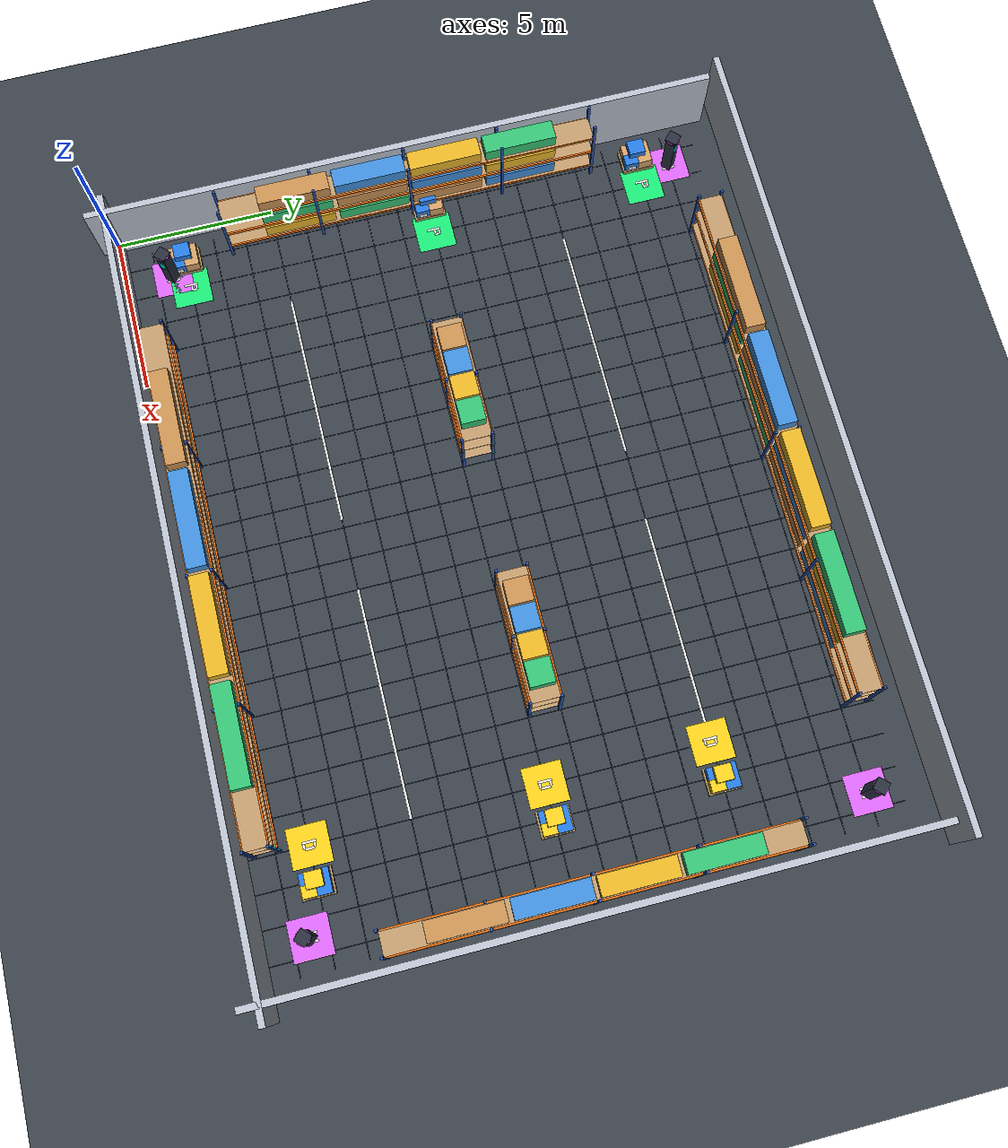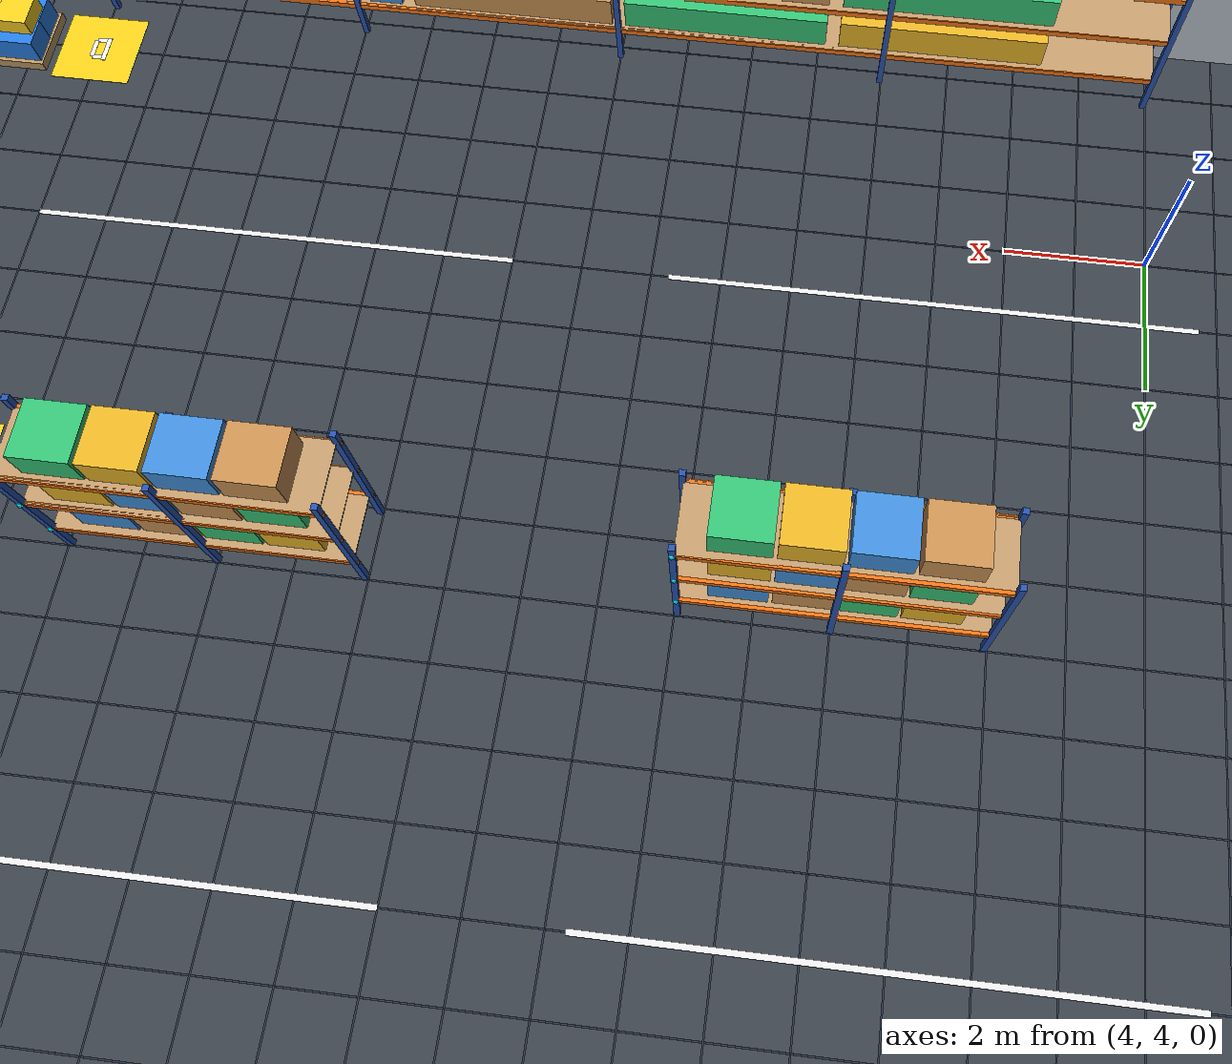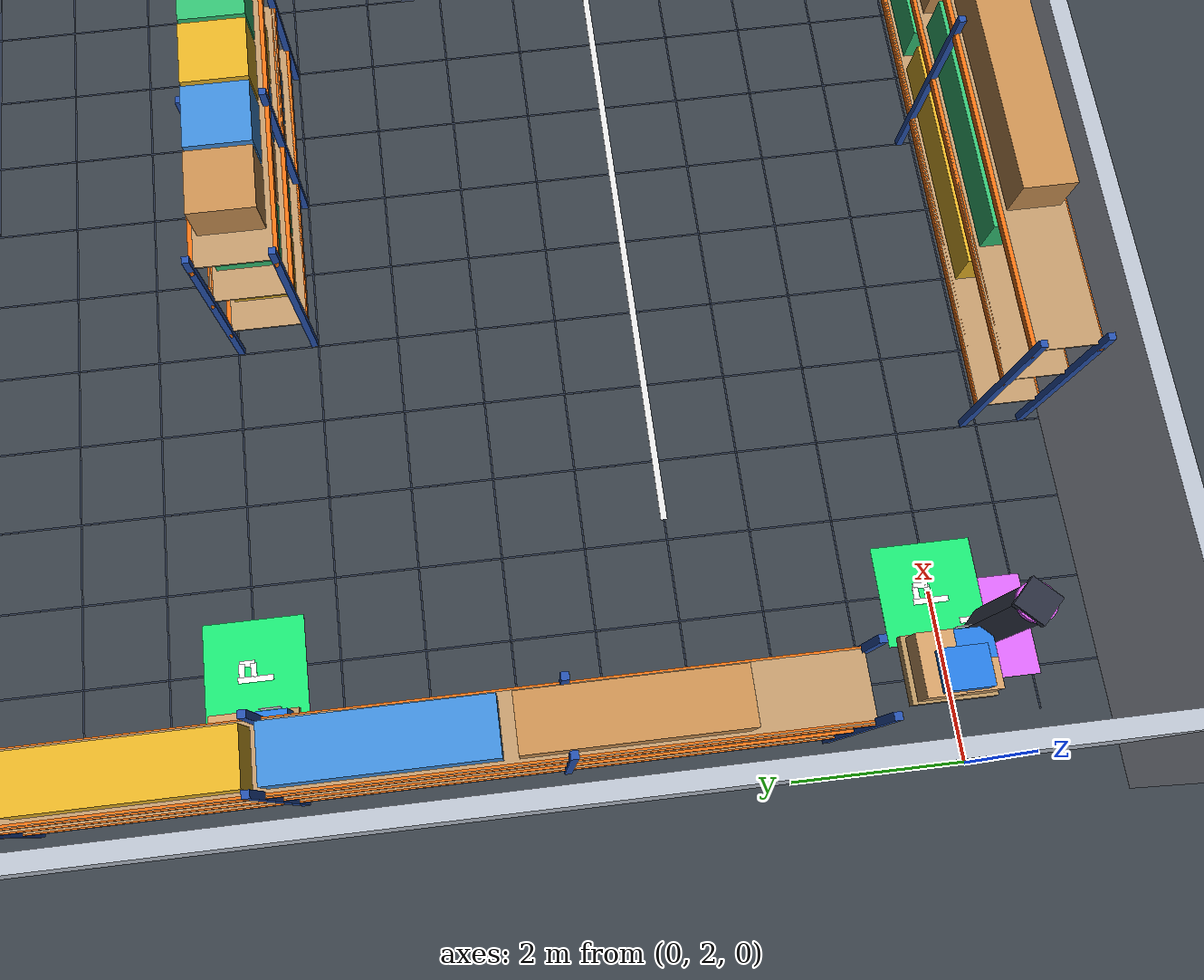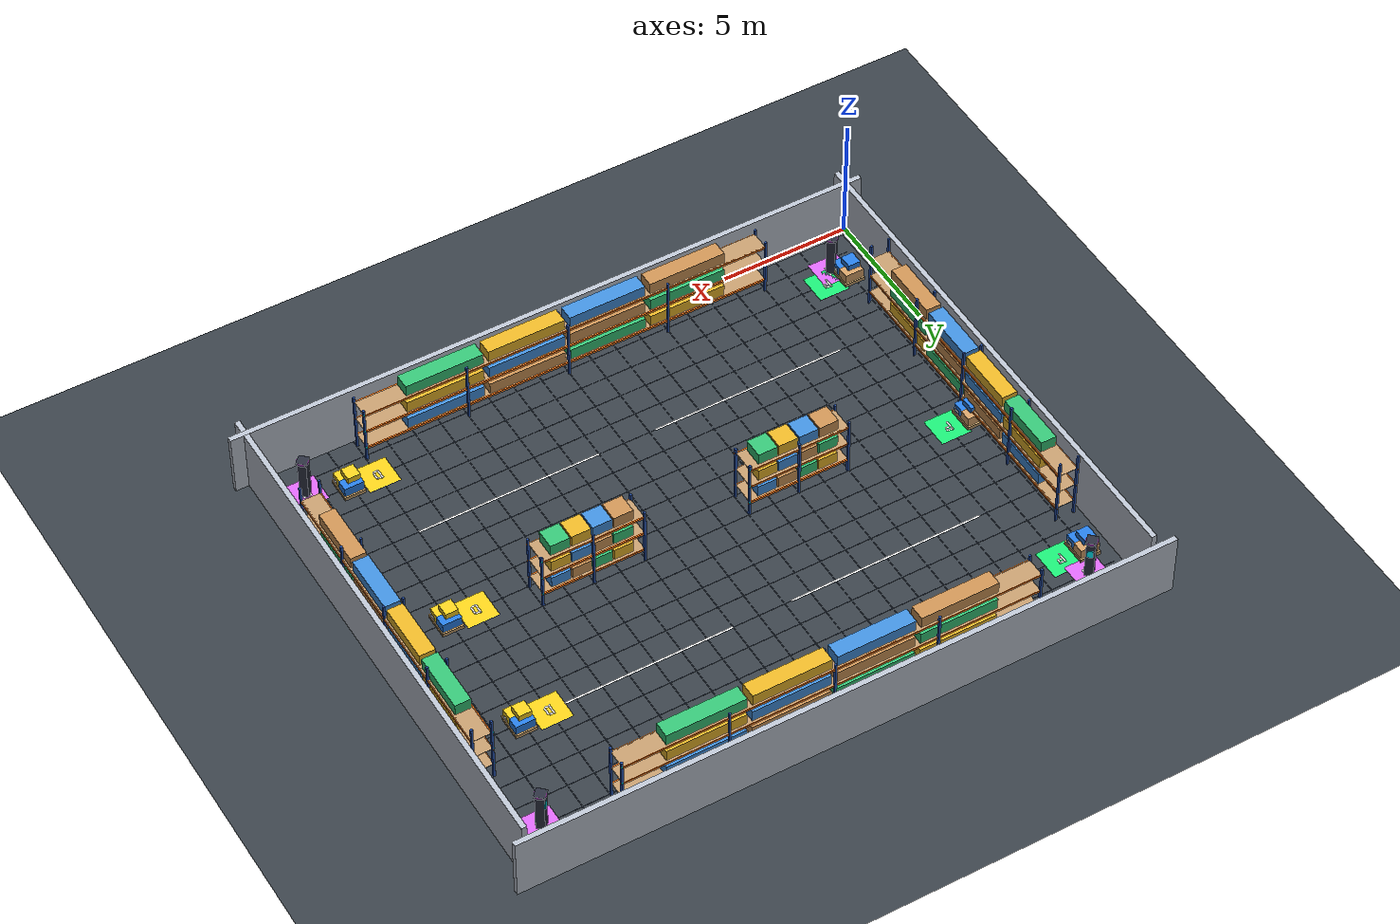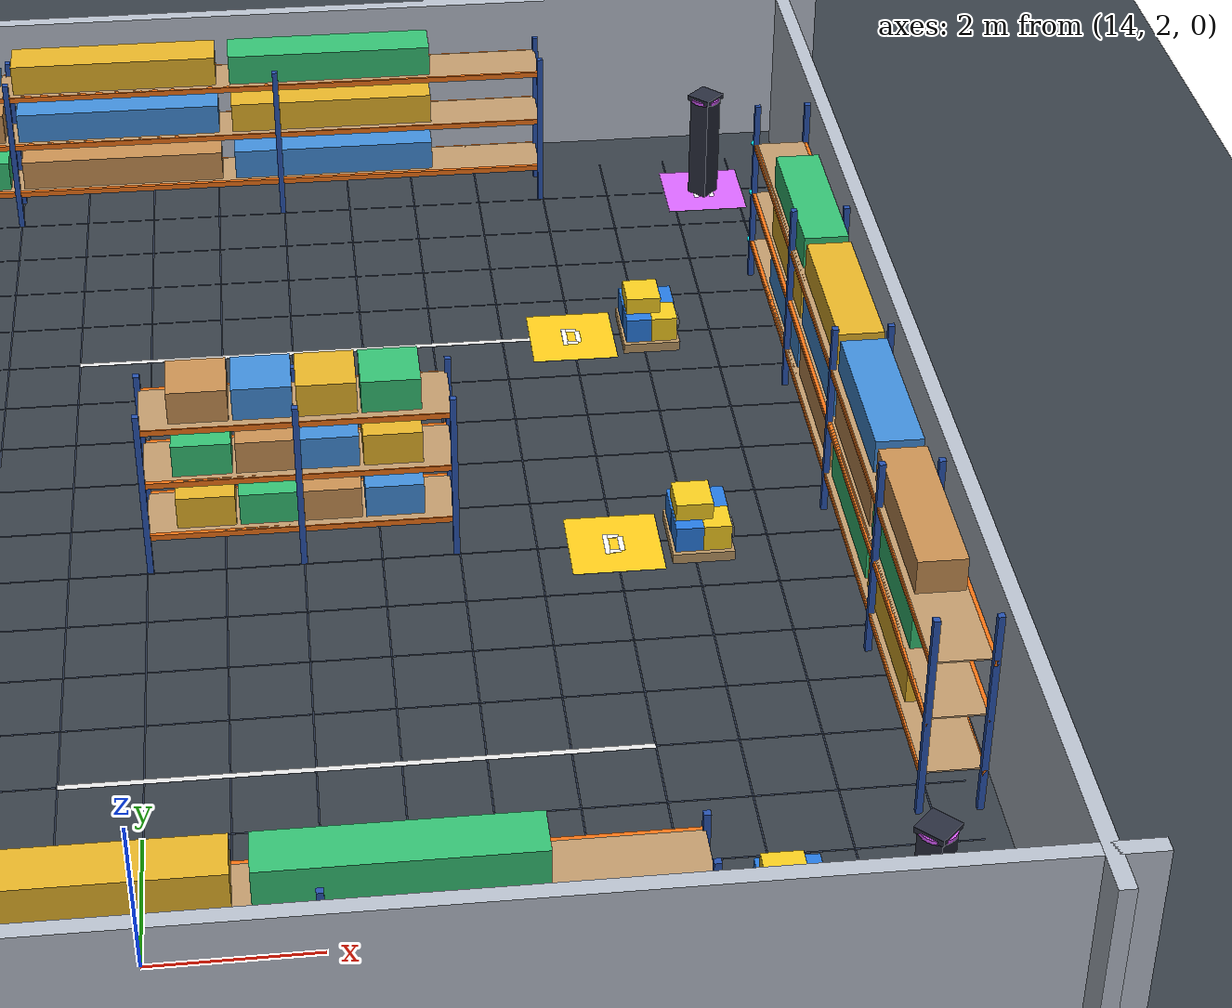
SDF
<?xml version="1.0" ?>
<sdf version="1.10">
  <world name="warehouse_s1">

    <!-- ── Physics ─────────────────────────────────────────────────────── -->
    <physics name="default" type="ode">
      <real_time_update_rate>0</real_time_update_rate>
      <max_step_size>0.01</max_step_size>
      <real_time_factor>1.0</real_time_factor>
      <ode>
        <solver>
          <type>quick</type>
          <iters>20</iters>
          <sor>1.3</sor>
        </solver>
        <constraints>
          <cfm>0</cfm>
          <erp>0.2</erp>
          <contact_max_correcting_vel>100</contact_max_correcting_vel>
          <contact_surface_layer>0.001</contact_surface_layer>
        </constraints>
      </ode>
    </physics>

    <!-- ── Plugins ─────────────────────────────────────────────────────── -->
    <plugin filename="gz-sim-physics-system" name="gz::sim::systems::Physics"/>
    <plugin filename="gz-sim-user-commands-system" name="gz::sim::systems::UserCommands"/>
    <plugin filename="gz-sim-scene-broadcaster-system" name="gz::sim::systems::SceneBroadcaster"/>
    <plugin filename="gz-sim-sensors-system" name="gz::sim::systems::Sensors">
      <render_engine>ogre2</render_engine>
    </plugin>
    <plugin filename="gz-sim-imu-system" name="gz::sim::systems::Imu"/>
    <plugin filename="gz-sim-contact-system" name="gz::sim::systems::Contact"/>

    <!-- ── Gravity ─────────────────────────────────────────────────────── -->
    <gravity>0 0 -9.81</gravity>
    <magnetic_field>6e-06 2.3e-05 -4.2e-05</magnetic_field>
    <atmosphere type="adiabatic"/>

    <!-- ── GUI ─────────────────────────────────────────────────────────── -->
    <gui fullscreen="0">
      <!-- 3D scene -->
      <plugin filename="MinimalScene" name="3D View">
        <gz-gui>
          <title>3D View</title>
          <property type="bool" key="showTitleBar">false</property>
          <property type="string" key="state">docked</property>
        </gz-gui>
        <engine>ogre</engine>
        <scene>scene</scene>
        <ambient_light>0.5 0.5 0.5</ambient_light>
        <background_color>0.7 0.7 0.7</background_color>
        <camera_pose>12.5 -3.5 15.0 0 0.85 1.5708</camera_pose>
      </plugin>

      <!-- Plugins that add functionality to the scene -->
      <plugin filename="EntityContextMenuPlugin" name="Entity context menu">
        <gz-gui>
          <property key="state" type="string">floating</property>
          <property key="width" type="double">5</property>
          <property key="height" type="double">5</property>
          <property key="showTitleBar" type="bool">false</property>
        </gz-gui>
      </plugin>
      <plugin filename="GzSceneManager" name="Scene Manager">
        <gz-gui>
          <property key="resizable" type="bool">false</property>
          <property key="width" type="double">5</property>
          <property key="height" type="double">5</property>
          <property key="state" type="string">floating</property>
          <property key="showTitleBar" type="bool">false</property>
        </gz-gui>
      </plugin>
      <plugin filename="InteractiveViewControl" name="Interactive view control">
        <gz-gui>
          <property key="resizable" type="bool">false</property>
          <property key="width" type="double">5</property>
          <property key="height" type="double">5</property>
          <property key="state" type="string">floating</property>
          <property key="showTitleBar" type="bool">false</property>
        </gz-gui>
      </plugin>
      <plugin filename="CameraTracking" name="Camera Tracking">
        <gz-gui>
          <property key="resizable" type="bool">false</property>
          <property key="width" type="double">5</property>
          <property key="height" type="double">5</property>
          <property key="state" type="string">floating</property>
          <property key="showTitleBar" type="bool">false</property>
        </gz-gui>
      </plugin>

      <!-- World control -->
      <plugin filename="WorldControl" name="World control">
        <gz-gui>
          <title>World control</title>
          <property type="bool" key="showTitleBar">false</property>
          <property type="bool" key="resizable">false</property>
          <property type="double" key="height">72</property>
          <property type="double" key="z">1</property>
          <property type="string" key="state">floating</property>
          <anchors target="3D View">
            <line own="left" target="left"/>
            <line own="bottom" target="bottom"/>
          </anchors>
        </gz-gui>
        <play_pause>true</play_pause>
        <step>true</step>
        <start_paused>false</start_paused>
        <use_event>true</use_event>
      </plugin>

      <!-- World statistics -->
      <plugin filename="WorldStats" name="World stats">
        <gz-gui>
          <title>World stats</title>
          <property type="bool" key="showTitleBar">false</property>
          <property type="bool" key="resizable">false</property>
          <property type="double" key="height">110</property>
          <property type="double" key="width">290</property>
          <property type="double" key="z">1</property>
          <property type="string" key="state">floating</property>
          <anchors target="3D View">
            <line own="right" target="right"/>
            <line own="bottom" target="bottom"/>
          </anchors>
        </gz-gui>
        <sim_time>true</sim_time>
        <real_time>true</real_time>
        <real_time_factor>true</real_time_factor>
        <iterations>true</iterations>
      </plugin>
    </gui>

    <!-- ── Scene ───────────────────────────────────────────────────────── -->
    <scene>
      <ambient>0.5 0.5 0.55 1</ambient>
      <background>0.12 0.15 0.18 1</background>
      <shadows>true</shadows>
      <grid>false</grid>
      <origin_visual>false</origin_visual>
    </scene>

    <!-- ── Sun ─────────────────────────────────────────────────────────── -->
    <light name="sun" type="directional">
      <cast_shadows>true</cast_shadows>
      <pose>0 0 10 0 0 0</pose>
      <diffuse>0.8 0.8 0.8 1</diffuse>
      <specular>0.2 0.2 0.2 1</specular>
      <attenuation>
        <range>1000</range>
        <constant>0.9</constant>
        <linear>0.01</linear>
        <quadratic>0.001</quadratic>
      </attenuation>
      <direction>-0.5 0.1 -0.9</direction>
    </light>

    <!-- ── Ground plane (25m × 20m warehouse floor) ─────────────────────── -->
    <model name="ground_plane">
      <static>true</static>
      <link name="link">
        <collision name="collision">
          <geometry>
            <plane>
              <normal>0 0 1</normal>
              <size>25 20</size>
            </plane>
          </geometry>
        </collision>
        <visual name="visual">
          <geometry>
            <plane>
              <normal>0 0 1</normal>
              <size>25 20</size>
            </plane>
          </geometry>
          <material>
            <ambient>0.22 0.25 0.28 1</ambient>
            <diffuse>0.22 0.25 0.28 1</diffuse>
            <specular>0.08 0.08 0.08 1</specular>
          </material>
        </visual>
        <pose>12.0 9.5 0 0 0 0</pose>
      </link>
    </model>

    <!-- ── Perimeter Walls (Industrial Silver) ────────────────────────── -->
    <!-- Wall geometry: 0.2m thick, 2.5m tall, placed on outer grid border -->

    <!-- West wall (x=0) -->
    <model name="wall_west">
      <static>true</static>
      <pose>0.1 9.5 1.25 0 0 0</pose>
      <link name="link">
        <collision name="collision">
          <geometry><box><size>0.2 20.0 2.5</size></box></geometry>
        </collision>
        <visual name="visual">
          <geometry><box><size>0.2 20.0 2.5</size></box></geometry>
          <material>
            <ambient>0.65 0.68 0.72 1</ambient>
            <diffuse>0.72 0.75 0.80 1</diffuse>
            <specular>0.15 0.15 0.15 1</specular>
          </material>
        </visual>
      </link>
    </model>

    <!-- East wall (x=24) -->
    <model name="wall_east">
      <static>true</static>
      <pose>23.9 9.5 1.25 0 0 0</pose>
      <link name="link">
        <collision name="collision">
          <geometry><box><size>0.2 20.0 2.5</size></box></geometry>
        </collision>
        <visual name="visual">
          <geometry><box><size>0.2 20.0 2.5</size></box></geometry>
          <material>
            <ambient>0.65 0.68 0.72 1</ambient>
            <diffuse>0.72 0.75 0.80 1</diffuse>
            <specular>0.15 0.15 0.15 1</specular>
          </material>
        </visual>
      </link>
    </model>

    <!-- South wall (y=0 grid → world y=19) -->
    <model name="wall_south">
      <static>true</static>
      <pose>12.0 19.9 1.25 0 0 0</pose>
      <link name="link">
        <collision name="collision">
          <geometry><box><size>25.0 0.2 2.5</size></box></geometry>
        </collision>
        <visual name="visual">
          <geometry><box><size>25.0 0.2 2.5</size></box></geometry>
          <material>
            <ambient>0.65 0.68 0.72 1</ambient>
            <diffuse>0.72 0.75 0.80 1</diffuse>
            <specular>0.15 0.15 0.15 1</specular>
          </material>
        </visual>
      </link>
    </model>

    <!-- North wall (y=19 grid → world y=0) -->
    <model name="wall_north">
      <static>true</static>
      <pose>12.0 0.1 1.25 0 0 0</pose>
      <link name="link">
        <collision name="collision">
          <geometry><box><size>25.0 0.2 2.5</size></box></geometry>
        </collision>
        <visual name="visual">
          <geometry><box><size>25.0 0.2 2.5</size></box></geometry>
          <material>
            <ambient>0.65 0.68 0.72 1</ambient>
            <diffuse>0.72 0.75 0.80 1</diffuse>
            <specular>0.15 0.15 0.15 1</specular>
          </material>
        </visual>
      </link>
    </model>

    <model name="floor_grid_telemetry">
      <static>true</static>
      <pose>0 0 0 0 0 0</pose>
      <link name="link">

        <visual name="grid_x_1">
          <pose>1.0 9.5 0.001 0 0 0</pose>
          <geometry><box><size>0.02 19.0 0.001</size></box></geometry>
          <material><ambient>0.14 0.18 0.24 1</ambient><diffuse>0.16 0.20 0.28 1</diffuse></material>
        </visual>

        <visual name="grid_x_2">
          <pose>2.0 9.5 0.001 0 0 0</pose>
          <geometry><box><size>0.02 19.0 0.001</size></box></geometry>
          <material><ambient>0.14 0.18 0.24 1</ambient><diffuse>0.16 0.20 0.28 1</diffuse></material>
        </visual>

        <visual name="grid_x_3">
          <pose>3.0 9.5 0.001 0 0 0</pose>
          <geometry><box><size>0.02 19.0 0.001</size></box></geometry>
          <material><ambient>0.14 0.18 0.24 1</ambient><diffuse>0.16 0.20 0.28 1</diffuse></material>
        </visual>

        <visual name="grid_x_4">
          <pose>4.0 9.5 0.001 0 0 0</pose>
          <geometry><box><size>0.02 19.0 0.001</size></box></geometry>
          <material><ambient>0.14 0.18 0.24 1</ambient><diffuse>0.16 0.20 0.28 1</diffuse></material>
        </visual>

        <visual name="grid_x_5">
          <pose>5.0 9.5 0.001 0 0 0</pose>
          <geometry><box><size>0.02 19.0 0.001</size></box></geometry>
          <material><ambient>0.14 0.18 0.24 1</ambient><diffuse>0.16 0.20 0.28 1</diffuse></material>
        </visual>

        <visual name="grid_x_6">
          <pose>6.0 9.5 0.001 0 0 0</pose>
          <geometry><box><size>0.02 19.0 0.001</size></box></geometry>
          <material><ambient>0.14 0.18 0.24 1</ambient><diffuse>0.16 0.20 0.28 1</diffuse></material>
        </visual>

        <visual name="grid_x_7">
          <pose>7.0 9.5 0.001 0 0 0</pose>
          <geometry><box><size>0.02 19.0 0.001</size></box></geometry>
          <material><ambient>0.14 0.18 0.24 1</ambient><diffuse>0.16 0.20 0.28 1</diffuse></material>
        </visual>

        <visual name="grid_x_8">
          <pose>8.0 9.5 0.001 0 0 0</pose>
          <geometry><box><size>0.02 19.0 0.001</size></box></geometry>
          <material><ambient>0.14 0.18 0.24 1</ambient><diffuse>0.16 0.20 0.28 1</diffuse></material>
        </visual>

        <visual name="grid_x_9">
          <pose>9.0 9.5 0.001 0 0 0</pose>
          <geometry><box><size>0.02 19.0 0.001</size></box></geometry>
          <material><ambient>0.14 0.18 0.24 1</ambient><diffuse>0.16 0.20 0.28 1</diffuse></material>
        </visual>

        <visual name="grid_x_10">
          <pose>10.0 9.5 0.001 0 0 0</pose>
          <geometry><box><size>0.02 19.0 0.001</size></box></geometry>
          <material><ambient>0.14 0.18 0.24 1</ambient><diffuse>0.16 0.20 0.28 1</diffuse></material>
        </visual>

        <visual name="grid_x_11">
          <pose>11.0 9.5 0.001 0 0 0</pose>
          <geometry><box><size>0.02 19.0 0.001</size></box></geometry>
          <material><ambient>0.14 0.18 0.24 1</ambient><diffuse>0.16 0.20 0.28 1</diffuse></material>
        </visual>

        <visual name="grid_x_12">
          <pose>12.0 9.5 0.001 0 0 0</pose>
          <geometry><box><size>0.02 19.0 0.001</size></box></geometry>
          <material><ambient>0.14 0.18 0.24 1</ambient><diffuse>0.16 0.20 0.28 1</diffuse></material>
        </visual>

        <visual name="grid_x_13">
          <pose>13.0 9.5 0.001 0 0 0</pose>
          <geometry><box><size>0.02 19.0 0.001</size></box></geometry>
          <material><ambient>0.14 0.18 0.24 1</ambient><diffuse>0.16 0.20 0.28 1</diffuse></material>
        </visual>

        <visual name="grid_x_14">
          <pose>14.0 9.5 0.001 0 0 0</pose>
          <geometry><box><size>0.02 19.0 0.001</size></box></geometry>
          <material><ambient>0.14 0.18 0.24 1</ambient><diffuse>0.16 0.20 0.28 1</diffuse></material>
        </visual>

        <visual name="grid_x_15">
          <pose>15.0 9.5 0.001 0 0 0</pose>
          <geometry><box><size>0.02 19.0 0.001</size></box></geometry>
          <material><ambient>0.14 0.18 0.24 1</ambient><diffuse>0.16 0.20 0.28 1</diffuse></material>
        </visual>

        <visual name="grid_x_16">
          <pose>16.0 9.5 0.001 0 0 0</pose>
          <geometry><box><size>0.02 19.0 0.001</size></box></geometry>
          <material><ambient>0.14 0.18 0.24 1</ambient><diffuse>0.16 0.20 0.28 1</diffuse></material>
        </visual>

        <visual name="grid_x_17">
          <pose>17.0 9.5 0.001 0 0 0</pose>
          <geometry><box><size>0.02 19.0 0.001</size></box></geometry>
          <material><ambient>0.14 0.18 0.24 1</ambient><diffuse>0.16 0.20 0.28 1</diffuse></material>
        </visual>

        <visual name="grid_x_18">
          <pose>18.0 9.5 0.001 0 0 0</pose>
          <geometry><box><size>0.02 19.0 0.001</size></box></geometry>
          <material><ambient>0.14 0.18 0.24 1</ambient><diffuse>0.16 0.20 0.28 1</diffuse></material>
        </visual>

        <visual name="grid_x_19">
          <pose>19.0 9.5 0.001 0 0 0</pose>
          <geometry><box><size>0.02 19.0 0.001</size></box></geometry>
          <material><ambient>0.14 0.18 0.24 1</ambient><diffuse>0.16 0.20 0.28 1</diffuse></material>
        </visual>

        <visual name="grid_x_20">
          <pose>20.0 9.5 0.001 0 0 0</pose>
          <geometry><box><size>0.02 19.0 0.001</size></box></geometry>
          <material><ambient>0.14 0.18 0.24 1</ambient><diffuse>0.16 0.20 0.28 1</diffuse></material>
        </visual>

        <visual name="grid_x_21">
          <pose>21.0 9.5 0.001 0 0 0</pose>
          <geometry><box><size>0.02 19.0 0.001</size></box></geometry>
          <material><ambient>0.14 0.18 0.24 1</ambient><diffuse>0.16 0.20 0.28 1</diffuse></material>
        </visual>

        <visual name="grid_x_22">
          <pose>22.0 9.5 0.001 0 0 0</pose>
          <geometry><box><size>0.02 19.0 0.001</size></box></geometry>
          <material><ambient>0.14 0.18 0.24 1</ambient><diffuse>0.16 0.20 0.28 1</diffuse></material>
        </visual>

        <visual name="grid_x_23">
          <pose>23.0 9.5 0.001 0 0 0</pose>
          <geometry><box><size>0.02 19.0 0.001</size></box></geometry>
          <material><ambient>0.14 0.18 0.24 1</ambient><diffuse>0.16 0.20 0.28 1</diffuse></material>
        </visual>

        <visual name="grid_y_1">
          <pose>12.0 1.0 0.001 0 0 0</pose>
          <geometry><box><size>23.0 0.02 0.001</size></box></geometry>
          <material><ambient>0.14 0.18 0.24 1</ambient><diffuse>0.16 0.20 0.28 1</diffuse></material>
        </visual>

        <visual name="grid_y_2">
          <pose>12.0 2.0 0.001 0 0 0</pose>
          <geometry><box><size>23.0 0.02 0.001</size></box></geometry>
          <material><ambient>0.14 0.18 0.24 1</ambient><diffuse>0.16 0.20 0.28 1</diffuse></material>
        </visual>

        <visual name="grid_y_3">
          <pose>12.0 3.0 0.001 0 0 0</pose>
          <geometry><box><size>23.0 0.02 0.001</size></box></geometry>
          <material><ambient>0.14 0.18 0.24 1</ambient><diffuse>0.16 0.20 0.28 1</diffuse></material>
        </visual>

        <visual name="grid_y_4">
          <pose>12.0 4.0 0.001 0 0 0</pose>
          <geometry><box><size>23.0 0.02 0.001</size></box></geometry>
          <material><ambient>0.14 0.18 0.24 1</ambient><diffuse>0.16 0.20 0.28 1</diffuse></material>
        </visual>

        <visual name="grid_y_5">
          <pose>12.0 5.0 0.001 0 0 0</pose>
          <geometry><box><size>23.0 0.02 0.001</size></box></geometry>
          <material><ambient>0.14 0.18 0.24 1</ambient><diffuse>0.16 0.20 0.28 1</diffuse></material>
        </visual>

        <visual name="grid_y_6">
          <pose>12.0 6.0 0.001 0 0 0</pose>
          <geometry><box><size>23.0 0.02 0.001</size></box></geometry>
          <material><ambient>0.14 0.18 0.24 1</ambient><diffuse>0.16 0.20 0.28 1</diffuse></material>
        </visual>

        <visual name="grid_y_7">
          <pose>12.0 7.0 0.001 0 0 0</pose>
          <geometry><box><size>23.0 0.02 0.001</size></box></geometry>
          <material><ambient>0.14 0.18 0.24 1</ambient><diffuse>0.16 0.20 0.28 1</diffuse></material>
        </visual>

        <visual name="grid_y_8">
          <pose>12.0 8.0 0.001 0 0 0</pose>
          <geometry><box><size>23.0 0.02 0.001</size></box></geometry>
          <material><ambient>0.14 0.18 0.24 1</ambient><diffuse>0.16 0.20 0.28 1</diffuse></material>
        </visual>

        <visual name="grid_y_9">
          <pose>12.0 9.0 0.001 0 0 0</pose>
          <geometry><box><size>23.0 0.02 0.001</size></box></geometry>
          <material><ambient>0.14 0.18 0.24 1</ambient><diffuse>0.16 0.20 0.28 1</diffuse></material>
        </visual>

        <visual name="grid_y_10">
          <pose>12.0 10.0 0.001 0 0 0</pose>
          <geometry><box><size>23.0 0.02 0.001</size></box></geometry>
          <material><ambient>0.14 0.18 0.24 1</ambient><diffuse>0.16 0.20 0.28 1</diffuse></material>
        </visual>

        <visual name="grid_y_11">
          <pose>12.0 11.0 0.001 0 0 0</pose>
          <geometry><box><size>23.0 0.02 0.001</size></box></geometry>
          <material><ambient>0.14 0.18 0.24 1</ambient><diffuse>0.16 0.20 0.28 1</diffuse></material>
        </visual>

        <visual name="grid_y_12">
          <pose>12.0 12.0 0.001 0 0 0</pose>
          <geometry><box><size>23.0 0.02 0.001</size></box></geometry>
          <material><ambient>0.14 0.18 0.24 1</ambient><diffuse>0.16 0.20 0.28 1</diffuse></material>
        </visual>

        <visual name="grid_y_13">
          <pose>12.0 13.0 0.001 0 0 0</pose>
          <geometry><box><size>23.0 0.02 0.001</size></box></geometry>
          <material><ambient>0.14 0.18 0.24 1</ambient><diffuse>0.16 0.20 0.28 1</diffuse></material>
        </visual>

        <visual name="grid_y_14">
          <pose>12.0 14.0 0.001 0 0 0</pose>
          <geometry><box><size>23.0 0.02 0.001</size></box></geometry>
          <material><ambient>0.14 0.18 0.24 1</ambient><diffuse>0.16 0.20 0.28 1</diffuse></material>
        </visual>

        <visual name="grid_y_15">
          <pose>12.0 15.0 0.001 0 0 0</pose>
          <geometry><box><size>23.0 0.02 0.001</size></box></geometry>
          <material><ambient>0.14 0.18 0.24 1</ambient><diffuse>0.16 0.20 0.28 1</diffuse></material>
        </visual>

        <visual name="grid_y_16">
          <pose>12.0 16.0 0.001 0 0 0</pose>
          <geometry><box><size>23.0 0.02 0.001</size></box></geometry>
          <material><ambient>0.14 0.18 0.24 1</ambient><diffuse>0.16 0.20 0.28 1</diffuse></material>
        </visual>

        <visual name="grid_y_17">
          <pose>12.0 17.0 0.001 0 0 0</pose>
          <geometry><box><size>23.0 0.02 0.001</size></box></geometry>
          <material><ambient>0.14 0.18 0.24 1</ambient><diffuse>0.16 0.20 0.28 1</diffuse></material>
        </visual>

        <visual name="grid_y_18">
          <pose>12.0 18.0 0.001 0 0 0</pose>
          <geometry><box><size>23.0 0.02 0.001</size></box></geometry>
          <material><ambient>0.14 0.18 0.24 1</ambient><diffuse>0.16 0.20 0.28 1</diffuse></material>
        </visual>
      </link>
    </model>

    <model name="transit_lanes">
      <static>true</static>
      <pose>0 0 0 0 0 0</pose>
      <link name="link">
<visual name="lane_north_west"><pose>7.0 14.0 0.002 0 0 0</pose><geometry><box><size>7.5 0.08 0.002</size></box></geometry><material><ambient>0.8 0.8 0.8 1</ambient><diffuse>0.9 0.9 0.9 1</diffuse></material></visual>
<visual name="lane_north_east"><pose>16.5 14.0 0.002 0 0 0</pose><geometry><box><size>7.0 0.08 0.002</size></box></geometry><material><ambient>0.8 0.8 0.8 1</ambient><diffuse>0.9 0.9 0.9 1</diffuse></material></visual>
<visual name="lane_south_west"><pose>7.0 5.0 0.002 0 0 0</pose><geometry><box><size>7.5 0.08 0.002</size></box></geometry><material><ambient>0.8 0.8 0.8 1</ambient><diffuse>0.9 0.9 0.9 1</diffuse></material></visual>
<visual name="lane_south_east"><pose>16.5 5.0 0.002 0 0 0</pose><geometry><box><size>7.0 0.08 0.002</size></box></geometry><material><ambient>0.8 0.8 0.8 1</ambient><diffuse>0.9 0.9 0.9 1</diffuse></material></visual>
      </link>
    </model>

    <model name="pad_s1_pickup_1">
      <static>true</static>
      <pose>2.000 17.000 0.003 0 0 0</pose>
      <link name="link">
        <visual name="pad_surface">
          <geometry><box><size>1.10 1.10 0.004</size></box></geometry>
          <material><ambient>0.05 0.50 0.28 1</ambient><diffuse>0.08 0.72 0.35 1</diffuse><specular>0.4 0.4 0.4 1</specular></material>
        </visual>
        <visual name="pad_border">
          <pose>0 0 0.002 0 0 0</pose>
          <geometry><box><size>1.20 1.20 0.002</size></box></geometry>
          <material><ambient>0.10 0.85 0.40 1</ambient><diffuse>0.10 0.90 0.45 1</diffuse></material>
        </visual>

        <visual name="stencil_p_vert"><pose>-0.10 0 0.005 0 0 0</pose><geometry><box><size>0.07 0.42 0.003</size></box></geometry><material><ambient>1 1 1 1</ambient><diffuse>1 1 1 1</diffuse><specular>0.5 0.5 0.5 1</specular></material></visual>
        <visual name="stencil_p_top"><pose>0.01 0.16 0.005 0 0 0</pose><geometry><box><size>0.16 0.07 0.003</size></box></geometry><material><ambient>1 1 1 1</ambient><diffuse>1 1 1 1</diffuse><specular>0.5 0.5 0.5 1</specular></material></visual>
        <visual name="stencil_p_mid"><pose>0.01 0.02 0.005 0 0 0</pose><geometry><box><size>0.16 0.07 0.003</size></box></geometry><material><ambient>1 1 1 1</ambient><diffuse>1 1 1 1</diffuse><specular>0.5 0.5 0.5 1</specular></material></visual>
        <visual name="stencil_p_right"><pose>0.09 0.09 0.005 0 0 0</pose><geometry><box><size>0.07 0.18 0.003</size></box></geometry><material><ambient>1 1 1 1</ambient><diffuse>1 1 1 1</diffuse><specular>0.5 0.5 0.5 1</specular></material></visual>
      </link>
    </model>

    <!-- Staged Pallet & Goods: s1_cargo_pickup_1 -->
    <model name="s1_cargo_pickup_1">
      <static>true</static>
      <pose>1.100 17.000 0.0 0 0 0.0000</pose>
      <link name="link">
        <!-- Wooden Euro Pallet Base (0.8m x 1.0m x 0.14m) -->
        <visual name="pallet_base">
          <pose>0 0 0.07 0 0 0</pose>
          <geometry><box><size>0.80 1.00 0.14</size></box></geometry>
          <material><ambient>0.58 0.46 0.30 1</ambient><diffuse>0.72 0.58 0.38 1</diffuse></material>
        </visual>
        <!-- Cargo Box Lower Left -->
        <visual name="box_ll">
          <pose>-0.18 -0.22 0.32 0 0 0</pose>
          <geometry><box><size>0.36 0.44 0.36</size></box></geometry>
          <material><ambient>0.72 0.52 0.32 1</ambient><diffuse>0.82 0.62 0.40 1</diffuse></material>
        </visual>
        <!-- Cargo Box Lower Right -->
        <visual name="box_lr">
          <pose>0.18 -0.22 0.32 0 0 0</pose>
          <geometry><box><size>0.36 0.44 0.36</size></box></geometry>
          <material><ambient>0.12 0.38 0.72 1</ambient><diffuse>0.15 0.48 0.88 1</diffuse><specular>0.3 0.3 0.3 1</specular></material>
        </visual>
        <!-- Cargo Box Top Container -->
        <visual name="box_top">
          <pose>0 0.22 0.32 0 0 0</pose>
          <geometry><box><size>0.74 0.44 0.36</size></box></geometry>
          <material><ambient>0.72 0.52 0.32 1</ambient><diffuse>0.82 0.62 0.40 1</diffuse></material>
        </visual>
        <!-- Upper Stacked Tote -->
        <visual name="box_upper">
          <pose>-0.10 0.0 0.62 0 0 0</pose>
          <geometry><box><size>0.48 0.52 0.24</size></box></geometry>
          <material><ambient>0.12 0.38 0.72 1</ambient><diffuse>0.15 0.48 0.88 1</diffuse><specular>0.3 0.3 0.3 1</specular></material>
        </visual>
        <!-- Barcode / Placard Label -->
        <visual name="placard">
          <pose>0.402 -0.22 0.32 0 0 0</pose>
          <geometry><box><size>0.005 0.24 0.16</size></box></geometry>
          <material><ambient>0.95 0.95 0.95 1</ambient><diffuse>0.98 0.98 0.98 1</diffuse></material>
        </visual>
      </link>
    </model>

    <model name="pad_s1_pickup_2">
      <static>true</static>
      <pose>2.000 10.000 0.003 0 0 0</pose>
      <link name="link">
        <visual name="pad_surface">
          <geometry><box><size>1.10 1.10 0.004</size></box></geometry>
          <material><ambient>0.05 0.50 0.28 1</ambient><diffuse>0.08 0.72 0.35 1</diffuse><specular>0.4 0.4 0.4 1</specular></material>
        </visual>
        <visual name="pad_border">
          <pose>0 0 0.002 0 0 0</pose>
          <geometry><box><size>1.20 1.20 0.002</size></box></geometry>
          <material><ambient>0.10 0.85 0.40 1</ambient><diffuse>0.10 0.90 0.45 1</diffuse></material>
        </visual>

        <visual name="stencil_p_vert"><pose>-0.10 0 0.005 0 0 0</pose><geometry><box><size>0.07 0.42 0.003</size></box></geometry><material><ambient>1 1 1 1</ambient><diffuse>1 1 1 1</diffuse><specular>0.5 0.5 0.5 1</specular></material></visual>
        <visual name="stencil_p_top"><pose>0.01 0.16 0.005 0 0 0</pose><geometry><box><size>0.16 0.07 0.003</size></box></geometry><material><ambient>1 1 1 1</ambient><diffuse>1 1 1 1</diffuse><specular>0.5 0.5 0.5 1</specular></material></visual>
        <visual name="stencil_p_mid"><pose>0.01 0.02 0.005 0 0 0</pose><geometry><box><size>0.16 0.07 0.003</size></box></geometry><material><ambient>1 1 1 1</ambient><diffuse>1 1 1 1</diffuse><specular>0.5 0.5 0.5 1</specular></material></visual>
        <visual name="stencil_p_right"><pose>0.09 0.09 0.005 0 0 0</pose><geometry><box><size>0.07 0.18 0.003</size></box></geometry><material><ambient>1 1 1 1</ambient><diffuse>1 1 1 1</diffuse><specular>0.5 0.5 0.5 1</specular></material></visual>
      </link>
    </model>

    <!-- Staged Pallet & Goods: s1_cargo_pickup_2 -->
    <model name="s1_cargo_pickup_2">
      <static>true</static>
      <pose>1.100 10.000 0.0 0 0 0.0000</pose>
      <link name="link">
        <!-- Wooden Euro Pallet Base (0.8m x 1.0m x 0.14m) -->
        <visual name="pallet_base">
          <pose>0 0 0.07 0 0 0</pose>
          <geometry><box><size>0.80 1.00 0.14</size></box></geometry>
          <material><ambient>0.58 0.46 0.30 1</ambient><diffuse>0.72 0.58 0.38 1</diffuse></material>
        </visual>
        <!-- Cargo Box Lower Left -->
        <visual name="box_ll">
          <pose>-0.18 -0.22 0.32 0 0 0</pose>
          <geometry><box><size>0.36 0.44 0.36</size></box></geometry>
          <material><ambient>0.72 0.52 0.32 1</ambient><diffuse>0.82 0.62 0.40 1</diffuse></material>
        </visual>
        <!-- Cargo Box Lower Right -->
        <visual name="box_lr">
          <pose>0.18 -0.22 0.32 0 0 0</pose>
          <geometry><box><size>0.36 0.44 0.36</size></box></geometry>
          <material><ambient>0.12 0.38 0.72 1</ambient><diffuse>0.15 0.48 0.88 1</diffuse><specular>0.3 0.3 0.3 1</specular></material>
        </visual>
        <!-- Cargo Box Top Container -->
        <visual name="box_top">
          <pose>0 0.22 0.32 0 0 0</pose>
          <geometry><box><size>0.74 0.44 0.36</size></box></geometry>
          <material><ambient>0.72 0.52 0.32 1</ambient><diffuse>0.82 0.62 0.40 1</diffuse></material>
        </visual>
        <!-- Upper Stacked Tote -->
        <visual name="box_upper">
          <pose>-0.10 0.0 0.62 0 0 0</pose>
          <geometry><box><size>0.48 0.52 0.24</size></box></geometry>
          <material><ambient>0.12 0.38 0.72 1</ambient><diffuse>0.15 0.48 0.88 1</diffuse><specular>0.3 0.3 0.3 1</specular></material>
        </visual>
        <!-- Barcode / Placard Label -->
        <visual name="placard">
          <pose>0.402 -0.22 0.32 0 0 0</pose>
          <geometry><box><size>0.005 0.24 0.16</size></box></geometry>
          <material><ambient>0.95 0.95 0.95 1</ambient><diffuse>0.98 0.98 0.98 1</diffuse></material>
        </visual>
      </link>
    </model>

    <model name="pad_s1_pickup_3">
      <static>true</static>
      <pose>2.000 2.000 0.003 0 0 0</pose>
      <link name="link">
        <visual name="pad_surface">
          <geometry><box><size>1.10 1.10 0.004</size></box></geometry>
          <material><ambient>0.05 0.50 0.28 1</ambient><diffuse>0.08 0.72 0.35 1</diffuse><specular>0.4 0.4 0.4 1</specular></material>
        </visual>
        <visual name="pad_border">
          <pose>0 0 0.002 0 0 0</pose>
          <geometry><box><size>1.20 1.20 0.002</size></box></geometry>
          <material><ambient>0.10 0.85 0.40 1</ambient><diffuse>0.10 0.90 0.45 1</diffuse></material>
        </visual>

        <visual name="stencil_p_vert"><pose>-0.10 0 0.005 0 0 0</pose><geometry><box><size>0.07 0.42 0.003</size></box></geometry><material><ambient>1 1 1 1</ambient><diffuse>1 1 1 1</diffuse><specular>0.5 0.5 0.5 1</specular></material></visual>
        <visual name="stencil_p_top"><pose>0.01 0.16 0.005 0 0 0</pose><geometry><box><size>0.16 0.07 0.003</size></box></geometry><material><ambient>1 1 1 1</ambient><diffuse>1 1 1 1</diffuse><specular>0.5 0.5 0.5 1</specular></material></visual>
        <visual name="stencil_p_mid"><pose>0.01 0.02 0.005 0 0 0</pose><geometry><box><size>0.16 0.07 0.003</size></box></geometry><material><ambient>1 1 1 1</ambient><diffuse>1 1 1 1</diffuse><specular>0.5 0.5 0.5 1</specular></material></visual>
        <visual name="stencil_p_right"><pose>0.09 0.09 0.005 0 0 0</pose><geometry><box><size>0.07 0.18 0.003</size></box></geometry><material><ambient>1 1 1 1</ambient><diffuse>1 1 1 1</diffuse><specular>0.5 0.5 0.5 1</specular></material></visual>
      </link>
    </model>

    <!-- Staged Pallet & Goods: s1_cargo_pickup_3 -->
    <model name="s1_cargo_pickup_3">
      <static>true</static>
      <pose>1.100 2.000 0.0 0 0 0.0000</pose>
      <link name="link">
        <!-- Wooden Euro Pallet Base (0.8m x 1.0m x 0.14m) -->
        <visual name="pallet_base">
          <pose>0 0 0.07 0 0 0</pose>
          <geometry><box><size>0.80 1.00 0.14</size></box></geometry>
          <material><ambient>0.58 0.46 0.30 1</ambient><diffuse>0.72 0.58 0.38 1</diffuse></material>
        </visual>
        <!-- Cargo Box Lower Left -->
        <visual name="box_ll">
          <pose>-0.18 -0.22 0.32 0 0 0</pose>
          <geometry><box><size>0.36 0.44 0.36</size></box></geometry>
          <material><ambient>0.72 0.52 0.32 1</ambient><diffuse>0.82 0.62 0.40 1</diffuse></material>
        </visual>
        <!-- Cargo Box Lower Right -->
        <visual name="box_lr">
          <pose>0.18 -0.22 0.32 0 0 0</pose>
          <geometry><box><size>0.36 0.44 0.36</size></box></geometry>
          <material><ambient>0.12 0.38 0.72 1</ambient><diffuse>0.15 0.48 0.88 1</diffuse><specular>0.3 0.3 0.3 1</specular></material>
        </visual>
        <!-- Cargo Box Top Container -->
        <visual name="box_top">
          <pose>0 0.22 0.32 0 0 0</pose>
          <geometry><box><size>0.74 0.44 0.36</size></box></geometry>
          <material><ambient>0.72 0.52 0.32 1</ambient><diffuse>0.82 0.62 0.40 1</diffuse></material>
        </visual>
        <!-- Upper Stacked Tote -->
        <visual name="box_upper">
          <pose>-0.10 0.0 0.62 0 0 0</pose>
          <geometry><box><size>0.48 0.52 0.24</size></box></geometry>
          <material><ambient>0.12 0.38 0.72 1</ambient><diffuse>0.15 0.48 0.88 1</diffuse><specular>0.3 0.3 0.3 1</specular></material>
        </visual>
        <!-- Barcode / Placard Label -->
        <visual name="placard">
          <pose>0.402 -0.22 0.32 0 0 0</pose>
          <geometry><box><size>0.005 0.24 0.16</size></box></geometry>
          <material><ambient>0.95 0.95 0.95 1</ambient><diffuse>0.98 0.98 0.98 1</diffuse></material>
        </visual>
      </link>
    </model>

    <model name="pad_s1_dropoff_1">
      <static>true</static>
      <pose>20.000 2.000 0.003 0 0 0</pose>
      <link name="link">
        <visual name="pad_surface">
          <geometry><box><size>1.10 1.10 0.004</size></box></geometry>
          <material><ambient>0.65 0.35 0.05 1</ambient><diffuse>0.90 0.55 0.08 1</diffuse><specular>0.4 0.4 0.4 1</specular></material>
        </visual>
        <visual name="pad_border">
          <pose>0 0 0.002 0 0 0</pose>
          <geometry><box><size>1.20 1.20 0.002</size></box></geometry>
          <material><ambient>0.98 0.75 0.08 1</ambient><diffuse>1.0 0.80 0.10 1</diffuse></material>
        </visual>

        <visual name="stencil_d_vert"><pose>-0.10 0 0.005 0 0 0</pose><geometry><box><size>0.07 0.42 0.003</size></box></geometry><material><ambient>1 1 1 1</ambient><diffuse>1 1 1 1</diffuse><specular>0.5 0.5 0.5 1</specular></material></visual>
        <visual name="stencil_d_top"><pose>0.0 0.16 0.005 0 0 0</pose><geometry><box><size>0.15 0.07 0.003</size></box></geometry><material><ambient>1 1 1 1</ambient><diffuse>1 1 1 1</diffuse><specular>0.5 0.5 0.5 1</specular></material></visual>
        <visual name="stencil_d_bot"><pose>0.0 -0.16 0.005 0 0 0</pose><geometry><box><size>0.15 0.07 0.003</size></box></geometry><material><ambient>1 1 1 1</ambient><diffuse>1 1 1 1</diffuse><specular>0.5 0.5 0.5 1</specular></material></visual>
        <visual name="stencil_d_right"><pose>0.09 0 0.005 0 0 0</pose><geometry><box><size>0.07 0.30 0.003</size></box></geometry><material><ambient>1 1 1 1</ambient><diffuse>1 1 1 1</diffuse><specular>0.5 0.5 0.5 1</specular></material></visual>
      </link>
    </model>

    <!-- Staged Pallet & Goods: s1_cargo_dropoff_1 -->
    <model name="s1_cargo_dropoff_1">
      <static>true</static>
      <pose>21.100 2.000 0.0 0 0 0.0000</pose>
      <link name="link">
        <!-- Wooden Euro Pallet Base (0.8m x 1.0m x 0.14m) -->
        <visual name="pallet_base">
          <pose>0 0 0.07 0 0 0</pose>
          <geometry><box><size>0.80 1.00 0.14</size></box></geometry>
          <material><ambient>0.58 0.46 0.30 1</ambient><diffuse>0.72 0.58 0.38 1</diffuse></material>
        </visual>
        <!-- Cargo Box Lower Left -->
        <visual name="box_ll">
          <pose>-0.18 -0.22 0.32 0 0 0</pose>
          <geometry><box><size>0.36 0.44 0.36</size></box></geometry>
          <material><ambient>0.12 0.38 0.72 1</ambient><diffuse>0.15 0.48 0.88 1</diffuse><specular>0.3 0.3 0.3 1</specular></material>
        </visual>
        <!-- Cargo Box Lower Right -->
        <visual name="box_lr">
          <pose>0.18 -0.22 0.32 0 0 0</pose>
          <geometry><box><size>0.36 0.44 0.36</size></box></geometry>
          <material><ambient>0.88 0.70 0.08 1</ambient><diffuse>0.96 0.80 0.12 1</diffuse></material>
        </visual>
        <!-- Cargo Box Top Container -->
        <visual name="box_top">
          <pose>0 0.22 0.32 0 0 0</pose>
          <geometry><box><size>0.74 0.44 0.36</size></box></geometry>
          <material><ambient>0.12 0.38 0.72 1</ambient><diffuse>0.15 0.48 0.88 1</diffuse><specular>0.3 0.3 0.3 1</specular></material>
        </visual>
        <!-- Upper Stacked Tote -->
        <visual name="box_upper">
          <pose>-0.10 0.0 0.62 0 0 0</pose>
          <geometry><box><size>0.48 0.52 0.24</size></box></geometry>
          <material><ambient>0.88 0.70 0.08 1</ambient><diffuse>0.96 0.80 0.12 1</diffuse></material>
        </visual>
        <!-- Barcode / Placard Label -->
        <visual name="placard">
          <pose>0.402 -0.22 0.32 0 0 0</pose>
          <geometry><box><size>0.005 0.24 0.16</size></box></geometry>
          <material><ambient>0.95 0.95 0.95 1</ambient><diffuse>0.98 0.98 0.98 1</diffuse></material>
        </visual>
      </link>
    </model>

    <model name="pad_s1_dropoff_2">
      <static>true</static>
      <pose>20.000 14.000 0.003 0 0 0</pose>
      <link name="link">
        <visual name="pad_surface">
          <geometry><box><size>1.10 1.10 0.004</size></box></geometry>
          <material><ambient>0.65 0.35 0.05 1</ambient><diffuse>0.90 0.55 0.08 1</diffuse><specular>0.4 0.4 0.4 1</specular></material>
        </visual>
        <visual name="pad_border">
          <pose>0 0 0.002 0 0 0</pose>
          <geometry><box><size>1.20 1.20 0.002</size></box></geometry>
          <material><ambient>0.98 0.75 0.08 1</ambient><diffuse>1.0 0.80 0.10 1</diffuse></material>
        </visual>

        <visual name="stencil_d_vert"><pose>-0.10 0 0.005 0 0 0</pose><geometry><box><size>0.07 0.42 0.003</size></box></geometry><material><ambient>1 1 1 1</ambient><diffuse>1 1 1 1</diffuse><specular>0.5 0.5 0.5 1</specular></material></visual>
        <visual name="stencil_d_top"><pose>0.0 0.16 0.005 0 0 0</pose><geometry><box><size>0.15 0.07 0.003</size></box></geometry><material><ambient>1 1 1 1</ambient><diffuse>1 1 1 1</diffuse><specular>0.5 0.5 0.5 1</specular></material></visual>
        <visual name="stencil_d_bot"><pose>0.0 -0.16 0.005 0 0 0</pose><geometry><box><size>0.15 0.07 0.003</size></box></geometry><material><ambient>1 1 1 1</ambient><diffuse>1 1 1 1</diffuse><specular>0.5 0.5 0.5 1</specular></material></visual>
        <visual name="stencil_d_right"><pose>0.09 0 0.005 0 0 0</pose><geometry><box><size>0.07 0.30 0.003</size></box></geometry><material><ambient>1 1 1 1</ambient><diffuse>1 1 1 1</diffuse><specular>0.5 0.5 0.5 1</specular></material></visual>
      </link>
    </model>

    <!-- Staged Pallet & Goods: s1_cargo_dropoff_2 -->
    <model name="s1_cargo_dropoff_2">
      <static>true</static>
      <pose>21.100 14.000 0.0 0 0 0.0000</pose>
      <link name="link">
        <!-- Wooden Euro Pallet Base (0.8m x 1.0m x 0.14m) -->
        <visual name="pallet_base">
          <pose>0 0 0.07 0 0 0</pose>
          <geometry><box><size>0.80 1.00 0.14</size></box></geometry>
          <material><ambient>0.58 0.46 0.30 1</ambient><diffuse>0.72 0.58 0.38 1</diffuse></material>
        </visual>
        <!-- Cargo Box Lower Left -->
        <visual name="box_ll">
          <pose>-0.18 -0.22 0.32 0 0 0</pose>
          <geometry><box><size>0.36 0.44 0.36</size></box></geometry>
          <material><ambient>0.12 0.38 0.72 1</ambient><diffuse>0.15 0.48 0.88 1</diffuse><specular>0.3 0.3 0.3 1</specular></material>
        </visual>
        <!-- Cargo Box Lower Right -->
        <visual name="box_lr">
          <pose>0.18 -0.22 0.32 0 0 0</pose>
          <geometry><box><size>0.36 0.44 0.36</size></box></geometry>
          <material><ambient>0.88 0.70 0.08 1</ambient><diffuse>0.96 0.80 0.12 1</diffuse></material>
        </visual>
        <!-- Cargo Box Top Container -->
        <visual name="box_top">
          <pose>0 0.22 0.32 0 0 0</pose>
          <geometry><box><size>0.74 0.44 0.36</size></box></geometry>
          <material><ambient>0.12 0.38 0.72 1</ambient><diffuse>0.15 0.48 0.88 1</diffuse><specular>0.3 0.3 0.3 1</specular></material>
        </visual>
        <!-- Upper Stacked Tote -->
        <visual name="box_upper">
          <pose>-0.10 0.0 0.62 0 0 0</pose>
          <geometry><box><size>0.48 0.52 0.24</size></box></geometry>
          <material><ambient>0.88 0.70 0.08 1</ambient><diffuse>0.96 0.80 0.12 1</diffuse></material>
        </visual>
        <!-- Barcode / Placard Label -->
        <visual name="placard">
          <pose>0.402 -0.22 0.32 0 0 0</pose>
          <geometry><box><size>0.005 0.24 0.16</size></box></geometry>
          <material><ambient>0.95 0.95 0.95 1</ambient><diffuse>0.98 0.98 0.98 1</diffuse></material>
        </visual>
      </link>
    </model>

    <model name="pad_s1_dropoff_3">
      <static>true</static>
      <pose>20.000 9.000 0.003 0 0 0</pose>
      <link name="link">
        <visual name="pad_surface">
          <geometry><box><size>1.10 1.10 0.004</size></box></geometry>
          <material><ambient>0.65 0.35 0.05 1</ambient><diffuse>0.90 0.55 0.08 1</diffuse><specular>0.4 0.4 0.4 1</specular></material>
        </visual>
        <visual name="pad_border">
          <pose>0 0 0.002 0 0 0</pose>
          <geometry><box><size>1.20 1.20 0.002</size></box></geometry>
          <material><ambient>0.98 0.75 0.08 1</ambient><diffuse>1.0 0.80 0.10 1</diffuse></material>
        </visual>

        <visual name="stencil_d_vert"><pose>-0.10 0 0.005 0 0 0</pose><geometry><box><size>0.07 0.42 0.003</size></box></geometry><material><ambient>1 1 1 1</ambient><diffuse>1 1 1 1</diffuse><specular>0.5 0.5 0.5 1</specular></material></visual>
        <visual name="stencil_d_top"><pose>0.0 0.16 0.005 0 0 0</pose><geometry><box><size>0.15 0.07 0.003</size></box></geometry><material><ambient>1 1 1 1</ambient><diffuse>1 1 1 1</diffuse><specular>0.5 0.5 0.5 1</specular></material></visual>
        <visual name="stencil_d_bot"><pose>0.0 -0.16 0.005 0 0 0</pose><geometry><box><size>0.15 0.07 0.003</size></box></geometry><material><ambient>1 1 1 1</ambient><diffuse>1 1 1 1</diffuse><specular>0.5 0.5 0.5 1</specular></material></visual>
        <visual name="stencil_d_right"><pose>0.09 0 0.005 0 0 0</pose><geometry><box><size>0.07 0.30 0.003</size></box></geometry><material><ambient>1 1 1 1</ambient><diffuse>1 1 1 1</diffuse><specular>0.5 0.5 0.5 1</specular></material></visual>
      </link>
    </model>

    <!-- Staged Pallet & Goods: s1_cargo_dropoff_3 -->
    <model name="s1_cargo_dropoff_3">
      <static>true</static>
      <pose>21.100 9.000 0.0 0 0 0.0000</pose>
      <link name="link">
        <!-- Wooden Euro Pallet Base (0.8m x 1.0m x 0.14m) -->
        <visual name="pallet_base">
          <pose>0 0 0.07 0 0 0</pose>
          <geometry><box><size>0.80 1.00 0.14</size></box></geometry>
          <material><ambient>0.58 0.46 0.30 1</ambient><diffuse>0.72 0.58 0.38 1</diffuse></material>
        </visual>
        <!-- Cargo Box Lower Left -->
        <visual name="box_ll">
          <pose>-0.18 -0.22 0.32 0 0 0</pose>
          <geometry><box><size>0.36 0.44 0.36</size></box></geometry>
          <material><ambient>0.12 0.38 0.72 1</ambient><diffuse>0.15 0.48 0.88 1</diffuse><specular>0.3 0.3 0.3 1</specular></material>
        </visual>
        <!-- Cargo Box Lower Right -->
        <visual name="box_lr">
          <pose>0.18 -0.22 0.32 0 0 0</pose>
          <geometry><box><size>0.36 0.44 0.36</size></box></geometry>
          <material><ambient>0.88 0.70 0.08 1</ambient><diffuse>0.96 0.80 0.12 1</diffuse></material>
        </visual>
        <!-- Cargo Box Top Container -->
        <visual name="box_top">
          <pose>0 0.22 0.32 0 0 0</pose>
          <geometry><box><size>0.74 0.44 0.36</size></box></geometry>
          <material><ambient>0.12 0.38 0.72 1</ambient><diffuse>0.15 0.48 0.88 1</diffuse><specular>0.3 0.3 0.3 1</specular></material>
        </visual>
        <!-- Upper Stacked Tote -->
        <visual name="box_upper">
          <pose>-0.10 0.0 0.62 0 0 0</pose>
          <geometry><box><size>0.48 0.52 0.24</size></box></geometry>
          <material><ambient>0.88 0.70 0.08 1</ambient><diffuse>0.96 0.80 0.12 1</diffuse></material>
        </visual>
        <!-- Barcode / Placard Label -->
        <visual name="placard">
          <pose>0.402 -0.22 0.32 0 0 0</pose>
          <geometry><box><size>0.005 0.24 0.16</size></box></geometry>
          <material><ambient>0.95 0.95 0.95 1</ambient><diffuse>0.98 0.98 0.98 1</diffuse></material>
        </visual>
      </link>
    </model>

    <model name="pad_s1_charge_nw">
      <static>true</static>
      <pose>1.500 18.000 0.003 0 0 0</pose>
      <link name="link">
        <visual name="pad_surface">
          <geometry><box><size>1.10 1.10 0.004</size></box></geometry>
          <material><ambient>0.40 0.15 0.65 1</ambient><diffuse>0.65 0.25 0.95 1</diffuse><specular>0.5 0.5 0.5 1</specular></material>
        </visual>
        <visual name="pad_border">
          <pose>0 0 0.002 0 0 0</pose>
          <geometry><box><size>1.20 1.20 0.002</size></box></geometry>
          <material><ambient>0.80 0.35 1.0 1</ambient><diffuse>0.85 0.40 1.0 1</diffuse></material>
        </visual>

        <visual name="stencil_h_left"><pose>-0.12 0 0.005 0 0 0</pose><geometry><box><size>0.07 0.42 0.003</size></box></geometry><material><ambient>1 1 1 1</ambient><diffuse>1 1 1 1</diffuse><specular>0.5 0.5 0.5 1</specular></material></visual>
        <visual name="stencil_h_right"><pose>0.12 0 0.005 0 0 0</pose><geometry><box><size>0.07 0.42 0.003</size></box></geometry><material><ambient>1 1 1 1</ambient><diffuse>1 1 1 1</diffuse><specular>0.5 0.5 0.5 1</specular></material></visual>
        <visual name="stencil_h_mid"><pose>0 0 0.005 0 0 0</pose><geometry><box><size>0.22 0.07 0.003</size></box></geometry><material><ambient>1 1 1 1</ambient><diffuse>1 1 1 1</diffuse><specular>0.5 0.5 0.5 1</specular></material></visual>
      </link>
    </model>

    <!-- Charging Kiosk: kiosk_s1_charge_nw -->
    <model name="kiosk_s1_charge_nw">
      <static>true</static>
      <pose>1.500 18.000 0.0 0 0 0.7850</pose>
      <link name="link">
        <!-- Main Pillar -->
        <visual name="pillar">
          <pose>0 0 0.80 0 0 0</pose>
          <geometry><box><size>0.32 0.32 1.60</size></box></geometry>
          <material><ambient>0.12 0.14 0.18 1</ambient><diffuse>0.16 0.18 0.24 1</diffuse><specular>0.4 0.4 0.4 1</specular></material>
        </visual>
        <!-- Power Cap -->
        <visual name="cap">
          <pose>0 0 1.64 0 0 0</pose>
          <geometry><box><size>0.38 0.38 0.08</size></box></geometry>
          <material><ambient>0.12 0.14 0.18 1</ambient><diffuse>0.16 0.18 0.24 1</diffuse><specular>0.4 0.4 0.4 1</specular></material>
        </visual>
        <!-- Glowing Purple Status Ring -->
        <visual name="halo_ring">
          <pose>0 0 1.61 0 0 0</pose>
          <geometry><cylinder><radius>0.22</radius><length>0.05</length></cylinder></geometry>
          <material><ambient>0.75 0.25 0.95 1</ambient><diffuse>0.85 0.35 1.0 1</diffuse><specular>1 1 1 1</specular></material>
        </visual>
        <!-- Diagnostic Telemetry Display Screen -->
        <visual name="screen">
          <pose>0.162 0 1.10 0 0 0</pose>
          <geometry><box><size>0.008 0.22 0.32</size></box></geometry>
          <material><ambient>0.0 0.85 1.0 1</ambient><diffuse>0.0 0.95 1.0 1</diffuse><specular>0.8 0.8 0.8 1</specular></material>
        </visual>
      </link>
    </model>

    <model name="pad_s1_charge_sw">
      <static>true</static>
      <pose>1.500 1.500 0.003 0 0 0</pose>
      <link name="link">
        <visual name="pad_surface">
          <geometry><box><size>1.10 1.10 0.004</size></box></geometry>
          <material><ambient>0.40 0.15 0.65 1</ambient><diffuse>0.65 0.25 0.95 1</diffuse><specular>0.5 0.5 0.5 1</specular></material>
        </visual>
        <visual name="pad_border">
          <pose>0 0 0.002 0 0 0</pose>
          <geometry><box><size>1.20 1.20 0.002</size></box></geometry>
          <material><ambient>0.80 0.35 1.0 1</ambient><diffuse>0.85 0.40 1.0 1</diffuse></material>
        </visual>

        <visual name="stencil_h_left"><pose>-0.12 0 0.005 0 0 0</pose><geometry><box><size>0.07 0.42 0.003</size></box></geometry><material><ambient>1 1 1 1</ambient><diffuse>1 1 1 1</diffuse><specular>0.5 0.5 0.5 1</specular></material></visual>
        <visual name="stencil_h_right"><pose>0.12 0 0.005 0 0 0</pose><geometry><box><size>0.07 0.42 0.003</size></box></geometry><material><ambient>1 1 1 1</ambient><diffuse>1 1 1 1</diffuse><specular>0.5 0.5 0.5 1</specular></material></visual>
        <visual name="stencil_h_mid"><pose>0 0 0.005 0 0 0</pose><geometry><box><size>0.22 0.07 0.003</size></box></geometry><material><ambient>1 1 1 1</ambient><diffuse>1 1 1 1</diffuse><specular>0.5 0.5 0.5 1</specular></material></visual>
      </link>
    </model>

    <!-- Charging Kiosk: kiosk_s1_charge_sw -->
    <model name="kiosk_s1_charge_sw">
      <static>true</static>
      <pose>1.500 1.500 0.0 0 0 -0.7850</pose>
      <link name="link">
        <!-- Main Pillar -->
        <visual name="pillar">
          <pose>0 0 0.80 0 0 0</pose>
          <geometry><box><size>0.32 0.32 1.60</size></box></geometry>
          <material><ambient>0.12 0.14 0.18 1</ambient><diffuse>0.16 0.18 0.24 1</diffuse><specular>0.4 0.4 0.4 1</specular></material>
        </visual>
        <!-- Power Cap -->
        <visual name="cap">
          <pose>0 0 1.64 0 0 0</pose>
          <geometry><box><size>0.38 0.38 0.08</size></box></geometry>
          <material><ambient>0.12 0.14 0.18 1</ambient><diffuse>0.16 0.18 0.24 1</diffuse><specular>0.4 0.4 0.4 1</specular></material>
        </visual>
        <!-- Glowing Purple Status Ring -->
        <visual name="halo_ring">
          <pose>0 0 1.61 0 0 0</pose>
          <geometry><cylinder><radius>0.22</radius><length>0.05</length></cylinder></geometry>
          <material><ambient>0.75 0.25 0.95 1</ambient><diffuse>0.85 0.35 1.0 1</diffuse><specular>1 1 1 1</specular></material>
        </visual>
        <!-- Diagnostic Telemetry Display Screen -->
        <visual name="screen">
          <pose>0.162 0 1.10 0 0 0</pose>
          <geometry><box><size>0.008 0.22 0.32</size></box></geometry>
          <material><ambient>0.0 0.85 1.0 1</ambient><diffuse>0.0 0.95 1.0 1</diffuse><specular>0.8 0.8 0.8 1</specular></material>
        </visual>
      </link>
    </model>

    <model name="pad_s1_charge_ne">
      <static>true</static>
      <pose>22.500 18.000 0.003 0 0 0</pose>
      <link name="link">
        <visual name="pad_surface">
          <geometry><box><size>1.10 1.10 0.004</size></box></geometry>
          <material><ambient>0.40 0.15 0.65 1</ambient><diffuse>0.65 0.25 0.95 1</diffuse><specular>0.5 0.5 0.5 1</specular></material>
        </visual>
        <visual name="pad_border">
          <pose>0 0 0.002 0 0 0</pose>
          <geometry><box><size>1.20 1.20 0.002</size></box></geometry>
          <material><ambient>0.80 0.35 1.0 1</ambient><diffuse>0.85 0.40 1.0 1</diffuse></material>
        </visual>

        <visual name="stencil_h_left"><pose>-0.12 0 0.005 0 0 0</pose><geometry><box><size>0.07 0.42 0.003</size></box></geometry><material><ambient>1 1 1 1</ambient><diffuse>1 1 1 1</diffuse><specular>0.5 0.5 0.5 1</specular></material></visual>
        <visual name="stencil_h_right"><pose>0.12 0 0.005 0 0 0</pose><geometry><box><size>0.07 0.42 0.003</size></box></geometry><material><ambient>1 1 1 1</ambient><diffuse>1 1 1 1</diffuse><specular>0.5 0.5 0.5 1</specular></material></visual>
        <visual name="stencil_h_mid"><pose>0 0 0.005 0 0 0</pose><geometry><box><size>0.22 0.07 0.003</size></box></geometry><material><ambient>1 1 1 1</ambient><diffuse>1 1 1 1</diffuse><specular>0.5 0.5 0.5 1</specular></material></visual>
      </link>
    </model>

    <!-- Charging Kiosk: kiosk_s1_charge_ne -->
    <model name="kiosk_s1_charge_ne">
      <static>true</static>
      <pose>22.500 18.000 0.0 0 0 2.3560</pose>
      <link name="link">
        <!-- Main Pillar -->
        <visual name="pillar">
          <pose>0 0 0.80 0 0 0</pose>
          <geometry><box><size>0.32 0.32 1.60</size></box></geometry>
          <material><ambient>0.12 0.14 0.18 1</ambient><diffuse>0.16 0.18 0.24 1</diffuse><specular>0.4 0.4 0.4 1</specular></material>
        </visual>
        <!-- Power Cap -->
        <visual name="cap">
          <pose>0 0 1.64 0 0 0</pose>
          <geometry><box><size>0.38 0.38 0.08</size></box></geometry>
          <material><ambient>0.12 0.14 0.18 1</ambient><diffuse>0.16 0.18 0.24 1</diffuse><specular>0.4 0.4 0.4 1</specular></material>
        </visual>
        <!-- Glowing Purple Status Ring -->
        <visual name="halo_ring">
          <pose>0 0 1.61 0 0 0</pose>
          <geometry><cylinder><radius>0.22</radius><length>0.05</length></cylinder></geometry>
          <material><ambient>0.75 0.25 0.95 1</ambient><diffuse>0.85 0.35 1.0 1</diffuse><specular>1 1 1 1</specular></material>
        </visual>
        <!-- Diagnostic Telemetry Display Screen -->
        <visual name="screen">
          <pose>0.162 0 1.10 0 0 0</pose>
          <geometry><box><size>0.008 0.22 0.32</size></box></geometry>
          <material><ambient>0.0 0.85 1.0 1</ambient><diffuse>0.0 0.95 1.0 1</diffuse><specular>0.8 0.8 0.8 1</specular></material>
        </visual>
      </link>
    </model>

    <model name="pad_s1_charge_se">
      <static>true</static>
      <pose>22.500 1.500 0.003 0 0 0</pose>
      <link name="link">
        <visual name="pad_surface">
          <geometry><box><size>1.10 1.10 0.004</size></box></geometry>
          <material><ambient>0.40 0.15 0.65 1</ambient><diffuse>0.65 0.25 0.95 1</diffuse><specular>0.5 0.5 0.5 1</specular></material>
        </visual>
        <visual name="pad_border">
          <pose>0 0 0.002 0 0 0</pose>
          <geometry><box><size>1.20 1.20 0.002</size></box></geometry>
          <material><ambient>0.80 0.35 1.0 1</ambient><diffuse>0.85 0.40 1.0 1</diffuse></material>
        </visual>

        <visual name="stencil_h_left"><pose>-0.12 0 0.005 0 0 0</pose><geometry><box><size>0.07 0.42 0.003</size></box></geometry><material><ambient>1 1 1 1</ambient><diffuse>1 1 1 1</diffuse><specular>0.5 0.5 0.5 1</specular></material></visual>
        <visual name="stencil_h_right"><pose>0.12 0 0.005 0 0 0</pose><geometry><box><size>0.07 0.42 0.003</size></box></geometry><material><ambient>1 1 1 1</ambient><diffuse>1 1 1 1</diffuse><specular>0.5 0.5 0.5 1</specular></material></visual>
        <visual name="stencil_h_mid"><pose>0 0 0.005 0 0 0</pose><geometry><box><size>0.22 0.07 0.003</size></box></geometry><material><ambient>1 1 1 1</ambient><diffuse>1 1 1 1</diffuse><specular>0.5 0.5 0.5 1</specular></material></visual>
      </link>
    </model>

    <!-- Charging Kiosk: kiosk_s1_charge_se -->
    <model name="kiosk_s1_charge_se">
      <static>true</static>
      <pose>22.500 1.500 0.0 0 0 -2.3560</pose>
      <link name="link">
        <!-- Main Pillar -->
        <visual name="pillar">
          <pose>0 0 0.80 0 0 0</pose>
          <geometry><box><size>0.32 0.32 1.60</size></box></geometry>
          <material><ambient>0.12 0.14 0.18 1</ambient><diffuse>0.16 0.18 0.24 1</diffuse><specular>0.4 0.4 0.4 1</specular></material>
        </visual>
        <!-- Power Cap -->
        <visual name="cap">
          <pose>0 0 1.64 0 0 0</pose>
          <geometry><box><size>0.38 0.38 0.08</size></box></geometry>
          <material><ambient>0.12 0.14 0.18 1</ambient><diffuse>0.16 0.18 0.24 1</diffuse><specular>0.4 0.4 0.4 1</specular></material>
        </visual>
        <!-- Glowing Purple Status Ring -->
        <visual name="halo_ring">
          <pose>0 0 1.61 0 0 0</pose>
          <geometry><cylinder><radius>0.22</radius><length>0.05</length></cylinder></geometry>
          <material><ambient>0.75 0.25 0.95 1</ambient><diffuse>0.85 0.35 1.0 1</diffuse><specular>1 1 1 1</specular></material>
        </visual>
        <!-- Diagnostic Telemetry Display Screen -->
        <visual name="screen">
          <pose>0.162 0 1.10 0 0 0</pose>
          <geometry><box><size>0.008 0.22 0.32</size></box></geometry>
          <material><ambient>0.0 0.85 1.0 1</ambient><diffuse>0.0 0.95 1.0 1</diffuse><specular>0.8 0.8 0.8 1</specular></material>
        </visual>
      </link>
    </model>

    <!-- Industrial Storage Rack: s1_rack_center_left -->
    <model name="s1_rack_center_left">
      <static>true</static>
      <pose>8.000 9.500 0.000 0 0 0.0000</pose>
      <link name="link">

        <visual name="post_1">
          <pose>-1.960 -0.460 1.200 0 0 0</pose>
          <geometry><box><size>0.08 0.08 2.400</size></box></geometry>
          <material><ambient>0.10 0.20 0.45 1</ambient><diffuse>0.15 0.32 0.68 1</diffuse><specular>0.3 0.3 0.3 1</specular></material>
        </visual>

        <visual name="post_2">
          <pose>-1.960 0.460 1.200 0 0 0</pose>
          <geometry><box><size>0.08 0.08 2.400</size></box></geometry>
          <material><ambient>0.10 0.20 0.45 1</ambient><diffuse>0.15 0.32 0.68 1</diffuse><specular>0.3 0.3 0.3 1</specular></material>
        </visual>

        <visual name="post_3">
          <pose>1.960 -0.460 1.200 0 0 0</pose>
          <geometry><box><size>0.08 0.08 2.400</size></box></geometry>
          <material><ambient>0.10 0.20 0.45 1</ambient><diffuse>0.15 0.32 0.68 1</diffuse><specular>0.3 0.3 0.3 1</specular></material>
        </visual>

        <visual name="post_4">
          <pose>1.960 0.460 1.200 0 0 0</pose>
          <geometry><box><size>0.08 0.08 2.400</size></box></geometry>
          <material><ambient>0.10 0.20 0.45 1</ambient><diffuse>0.15 0.32 0.68 1</diffuse><specular>0.3 0.3 0.3 1</specular></material>
        </visual>

        <visual name="post_5">
          <pose>0.000 -0.460 1.200 0 0 0</pose>
          <geometry><box><size>0.08 0.08 2.400</size></box></geometry>
          <material><ambient>0.10 0.20 0.45 1</ambient><diffuse>0.15 0.32 0.68 1</diffuse><specular>0.3 0.3 0.3 1</specular></material>
        </visual>

        <visual name="post_6">
          <pose>0.000 0.460 1.200 0 0 0</pose>
          <geometry><box><size>0.08 0.08 2.400</size></box></geometry>
          <material><ambient>0.10 0.20 0.45 1</ambient><diffuse>0.15 0.32 0.68 1</diffuse><specular>0.3 0.3 0.3 1</specular></material>
        </visual>

        <visual name="beam_front_1">
          <pose>0 -0.460 0.550 0 0 0</pose>
          <geometry><box><size>4.000 0.05 0.08</size></box></geometry>
          <material><ambient>0.85 0.35 0.05 1</ambient><diffuse>0.95 0.45 0.08 1</diffuse><specular>0.2 0.2 0.2 1</specular></material>
        </visual>
        <visual name="beam_back_1">
          <pose>0 0.460 0.550 0 0 0</pose>
          <geometry><box><size>4.000 0.05 0.08</size></box></geometry>
          <material><ambient>0.85 0.35 0.05 1</ambient><diffuse>0.95 0.45 0.08 1</diffuse><specular>0.2 0.2 0.2 1</specular></material>
        </visual>
        <visual name="deck_1">
          <pose>0 0 0.580 0 0 0</pose>
          <geometry><box><size>3.900 0.940 0.02</size></box></geometry>
          <material><ambient>0.60 0.48 0.32 1</ambient><diffuse>0.75 0.60 0.42 1</diffuse><specular>0.1 0.1 0.1 1</specular></material>
        </visual>

        <visual name="cargo_t1_b1">
          <pose>-1.200 0 0.825 0 0 0</pose>
          <geometry><box><size>0.750 0.750 0.450</size></box></geometry>
          <material><ambient>0.75 0.55 0.10 1</ambient><diffuse>0.90 0.70 0.15 1</diffuse></material>
        </visual>

        <visual name="cargo_t1_b2">
          <pose>-0.400 0 0.825 0 0 0</pose>
          <geometry><box><size>0.750 0.750 0.450</size></box></geometry>
          <material><ambient>0.15 0.60 0.35 1</ambient><diffuse>0.20 0.75 0.45 1</diffuse></material>
        </visual>

        <visual name="cargo_t1_b3">
          <pose>0.400 0 0.825 0 0 0</pose>
          <geometry><box><size>0.750 0.750 0.450</size></box></geometry>
          <material><ambient>0.65 0.45 0.25 1</ambient><diffuse>0.78 0.56 0.32 1</diffuse></material>
        </visual>

        <visual name="cargo_t1_b4">
          <pose>1.200 0 0.825 0 0 0</pose>
          <geometry><box><size>0.750 0.750 0.450</size></box></geometry>
          <material><ambient>0.20 0.45 0.70 1</ambient><diffuse>0.25 0.55 0.85 1</diffuse></material>
        </visual>

        <visual name="led_indicator_1">
          <pose>1.960 0.500 0.600 0 0 0</pose>
          <geometry><sphere><radius>0.035</radius></sphere></geometry>
          <material><ambient>0.0 0.85 1.0 1</ambient><diffuse>0.0 0.95 1.0 1</diffuse><specular>1 1 1 1</specular></material>
        </visual>

        <visual name="beam_front_2">
          <pose>0 -0.460 1.350 0 0 0</pose>
          <geometry><box><size>4.000 0.05 0.08</size></box></geometry>
          <material><ambient>0.85 0.35 0.05 1</ambient><diffuse>0.95 0.45 0.08 1</diffuse><specular>0.2 0.2 0.2 1</specular></material>
        </visual>
        <visual name="beam_back_2">
          <pose>0 0.460 1.350 0 0 0</pose>
          <geometry><box><size>4.000 0.05 0.08</size></box></geometry>
          <material><ambient>0.85 0.35 0.05 1</ambient><diffuse>0.95 0.45 0.08 1</diffuse><specular>0.2 0.2 0.2 1</specular></material>
        </visual>
        <visual name="deck_2">
          <pose>0 0 1.380 0 0 0</pose>
          <geometry><box><size>3.900 0.940 0.02</size></box></geometry>
          <material><ambient>0.60 0.48 0.32 1</ambient><diffuse>0.75 0.60 0.42 1</diffuse><specular>0.1 0.1 0.1 1</specular></material>
        </visual>

        <visual name="cargo_t2_b1">
          <pose>-1.200 0 1.625 0 0 0</pose>
          <geometry><box><size>0.750 0.750 0.450</size></box></geometry>
          <material><ambient>0.15 0.60 0.35 1</ambient><diffuse>0.20 0.75 0.45 1</diffuse></material>
        </visual>

        <visual name="cargo_t2_b2">
          <pose>-0.400 0 1.625 0 0 0</pose>
          <geometry><box><size>0.750 0.750 0.450</size></box></geometry>
          <material><ambient>0.65 0.45 0.25 1</ambient><diffuse>0.78 0.56 0.32 1</diffuse></material>
        </visual>

        <visual name="cargo_t2_b3">
          <pose>0.400 0 1.625 0 0 0</pose>
          <geometry><box><size>0.750 0.750 0.450</size></box></geometry>
          <material><ambient>0.20 0.45 0.70 1</ambient><diffuse>0.25 0.55 0.85 1</diffuse></material>
        </visual>

        <visual name="cargo_t2_b4">
          <pose>1.200 0 1.625 0 0 0</pose>
          <geometry><box><size>0.750 0.750 0.450</size></box></geometry>
          <material><ambient>0.75 0.55 0.10 1</ambient><diffuse>0.90 0.70 0.15 1</diffuse></material>
        </visual>

        <visual name="led_indicator_2">
          <pose>1.960 0.500 1.400 0 0 0</pose>
          <geometry><sphere><radius>0.035</radius></sphere></geometry>
          <material><ambient>0.0 0.85 1.0 1</ambient><diffuse>0.0 0.95 1.0 1</diffuse><specular>1 1 1 1</specular></material>
        </visual>

        <visual name="beam_front_3">
          <pose>0 -0.460 2.150 0 0 0</pose>
          <geometry><box><size>4.000 0.05 0.08</size></box></geometry>
          <material><ambient>0.85 0.35 0.05 1</ambient><diffuse>0.95 0.45 0.08 1</diffuse><specular>0.2 0.2 0.2 1</specular></material>
        </visual>
        <visual name="beam_back_3">
          <pose>0 0.460 2.150 0 0 0</pose>
          <geometry><box><size>4.000 0.05 0.08</size></box></geometry>
          <material><ambient>0.85 0.35 0.05 1</ambient><diffuse>0.95 0.45 0.08 1</diffuse><specular>0.2 0.2 0.2 1</specular></material>
        </visual>
        <visual name="deck_3">
          <pose>0 0 2.180 0 0 0</pose>
          <geometry><box><size>3.900 0.940 0.02</size></box></geometry>
          <material><ambient>0.60 0.48 0.32 1</ambient><diffuse>0.75 0.60 0.42 1</diffuse><specular>0.1 0.1 0.1 1</specular></material>
        </visual>

        <visual name="cargo_t3_b1">
          <pose>-1.200 0 2.425 0 0 0</pose>
          <geometry><box><size>0.750 0.750 0.450</size></box></geometry>
          <material><ambient>0.65 0.45 0.25 1</ambient><diffuse>0.78 0.56 0.32 1</diffuse></material>
        </visual>

        <visual name="cargo_t3_b2">
          <pose>-0.400 0 2.425 0 0 0</pose>
          <geometry><box><size>0.750 0.750 0.450</size></box></geometry>
          <material><ambient>0.20 0.45 0.70 1</ambient><diffuse>0.25 0.55 0.85 1</diffuse></material>
        </visual>

        <visual name="cargo_t3_b3">
          <pose>0.400 0 2.425 0 0 0</pose>
          <geometry><box><size>0.750 0.750 0.450</size></box></geometry>
          <material><ambient>0.75 0.55 0.10 1</ambient><diffuse>0.90 0.70 0.15 1</diffuse></material>
        </visual>

        <visual name="cargo_t3_b4">
          <pose>1.200 0 2.425 0 0 0</pose>
          <geometry><box><size>0.750 0.750 0.450</size></box></geometry>
          <material><ambient>0.15 0.60 0.35 1</ambient><diffuse>0.20 0.75 0.45 1</diffuse></material>
        </visual>

        <visual name="led_indicator_3">
          <pose>1.960 0.500 2.200 0 0 0</pose>
          <geometry><sphere><radius>0.035</radius></sphere></geometry>
          <material><ambient>0.0 0.85 1.0 1</ambient><diffuse>0.0 0.95 1.0 1</diffuse><specular>1 1 1 1</specular></material>
        </visual>
      </link>
    </model>

    <!-- Industrial Storage Rack: s1_rack_center_right -->
    <model name="s1_rack_center_right">
      <static>true</static>
      <pose>16.000 9.500 0.000 0 0 0.0000</pose>
      <link name="link">

        <visual name="post_1">
          <pose>-1.960 -0.460 1.200 0 0 0</pose>
          <geometry><box><size>0.08 0.08 2.400</size></box></geometry>
          <material><ambient>0.10 0.20 0.45 1</ambient><diffuse>0.15 0.32 0.68 1</diffuse><specular>0.3 0.3 0.3 1</specular></material>
        </visual>

        <visual name="post_2">
          <pose>-1.960 0.460 1.200 0 0 0</pose>
          <geometry><box><size>0.08 0.08 2.400</size></box></geometry>
          <material><ambient>0.10 0.20 0.45 1</ambient><diffuse>0.15 0.32 0.68 1</diffuse><specular>0.3 0.3 0.3 1</specular></material>
        </visual>

        <visual name="post_3">
          <pose>1.960 -0.460 1.200 0 0 0</pose>
          <geometry><box><size>0.08 0.08 2.400</size></box></geometry>
          <material><ambient>0.10 0.20 0.45 1</ambient><diffuse>0.15 0.32 0.68 1</diffuse><specular>0.3 0.3 0.3 1</specular></material>
        </visual>

        <visual name="post_4">
          <pose>1.960 0.460 1.200 0 0 0</pose>
          <geometry><box><size>0.08 0.08 2.400</size></box></geometry>
          <material><ambient>0.10 0.20 0.45 1</ambient><diffuse>0.15 0.32 0.68 1</diffuse><specular>0.3 0.3 0.3 1</specular></material>
        </visual>

        <visual name="post_5">
          <pose>0.000 -0.460 1.200 0 0 0</pose>
          <geometry><box><size>0.08 0.08 2.400</size></box></geometry>
          <material><ambient>0.10 0.20 0.45 1</ambient><diffuse>0.15 0.32 0.68 1</diffuse><specular>0.3 0.3 0.3 1</specular></material>
        </visual>

        <visual name="post_6">
          <pose>0.000 0.460 1.200 0 0 0</pose>
          <geometry><box><size>0.08 0.08 2.400</size></box></geometry>
          <material><ambient>0.10 0.20 0.45 1</ambient><diffuse>0.15 0.32 0.68 1</diffuse><specular>0.3 0.3 0.3 1</specular></material>
        </visual>

        <visual name="beam_front_1">
          <pose>0 -0.460 0.550 0 0 0</pose>
          <geometry><box><size>4.000 0.05 0.08</size></box></geometry>
          <material><ambient>0.85 0.35 0.05 1</ambient><diffuse>0.95 0.45 0.08 1</diffuse><specular>0.2 0.2 0.2 1</specular></material>
        </visual>
        <visual name="beam_back_1">
          <pose>0 0.460 0.550 0 0 0</pose>
          <geometry><box><size>4.000 0.05 0.08</size></box></geometry>
          <material><ambient>0.85 0.35 0.05 1</ambient><diffuse>0.95 0.45 0.08 1</diffuse><specular>0.2 0.2 0.2 1</specular></material>
        </visual>
        <visual name="deck_1">
          <pose>0 0 0.580 0 0 0</pose>
          <geometry><box><size>3.900 0.940 0.02</size></box></geometry>
          <material><ambient>0.60 0.48 0.32 1</ambient><diffuse>0.75 0.60 0.42 1</diffuse><specular>0.1 0.1 0.1 1</specular></material>
        </visual>

        <visual name="cargo_t1_b1">
          <pose>-1.200 0 0.825 0 0 0</pose>
          <geometry><box><size>0.750 0.750 0.450</size></box></geometry>
          <material><ambient>0.75 0.55 0.10 1</ambient><diffuse>0.90 0.70 0.15 1</diffuse></material>
        </visual>

        <visual name="cargo_t1_b2">
          <pose>-0.400 0 0.825 0 0 0</pose>
          <geometry><box><size>0.750 0.750 0.450</size></box></geometry>
          <material><ambient>0.15 0.60 0.35 1</ambient><diffuse>0.20 0.75 0.45 1</diffuse></material>
        </visual>

        <visual name="cargo_t1_b3">
          <pose>0.400 0 0.825 0 0 0</pose>
          <geometry><box><size>0.750 0.750 0.450</size></box></geometry>
          <material><ambient>0.65 0.45 0.25 1</ambient><diffuse>0.78 0.56 0.32 1</diffuse></material>
        </visual>

        <visual name="cargo_t1_b4">
          <pose>1.200 0 0.825 0 0 0</pose>
          <geometry><box><size>0.750 0.750 0.450</size></box></geometry>
          <material><ambient>0.20 0.45 0.70 1</ambient><diffuse>0.25 0.55 0.85 1</diffuse></material>
        </visual>

        <visual name="led_indicator_1">
          <pose>1.960 0.500 0.600 0 0 0</pose>
          <geometry><sphere><radius>0.035</radius></sphere></geometry>
          <material><ambient>0.0 0.85 1.0 1</ambient><diffuse>0.0 0.95 1.0 1</diffuse><specular>1 1 1 1</specular></material>
        </visual>

        <visual name="beam_front_2">
          <pose>0 -0.460 1.350 0 0 0</pose>
          <geometry><box><size>4.000 0.05 0.08</size></box></geometry>
          <material><ambient>0.85 0.35 0.05 1</ambient><diffuse>0.95 0.45 0.08 1</diffuse><specular>0.2 0.2 0.2 1</specular></material>
        </visual>
        <visual name="beam_back_2">
          <pose>0 0.460 1.350 0 0 0</pose>
          <geometry><box><size>4.000 0.05 0.08</size></box></geometry>
          <material><ambient>0.85 0.35 0.05 1</ambient><diffuse>0.95 0.45 0.08 1</diffuse><specular>0.2 0.2 0.2 1</specular></material>
        </visual>
        <visual name="deck_2">
          <pose>0 0 1.380 0 0 0</pose>
          <geometry><box><size>3.900 0.940 0.02</size></box></geometry>
          <material><ambient>0.60 0.48 0.32 1</ambient><diffuse>0.75 0.60 0.42 1</diffuse><specular>0.1 0.1 0.1 1</specular></material>
        </visual>

        <visual name="cargo_t2_b1">
          <pose>-1.200 0 1.625 0 0 0</pose>
          <geometry><box><size>0.750 0.750 0.450</size></box></geometry>
          <material><ambient>0.15 0.60 0.35 1</ambient><diffuse>0.20 0.75 0.45 1</diffuse></material>
        </visual>

        <visual name="cargo_t2_b2">
          <pose>-0.400 0 1.625 0 0 0</pose>
          <geometry><box><size>0.750 0.750 0.450</size></box></geometry>
          <material><ambient>0.65 0.45 0.25 1</ambient><diffuse>0.78 0.56 0.32 1</diffuse></material>
        </visual>

        <visual name="cargo_t2_b3">
          <pose>0.400 0 1.625 0 0 0</pose>
          <geometry><box><size>0.750 0.750 0.450</size></box></geometry>
          <material><ambient>0.20 0.45 0.70 1</ambient><diffuse>0.25 0.55 0.85 1</diffuse></material>
        </visual>

        <visual name="cargo_t2_b4">
          <pose>1.200 0 1.625 0 0 0</pose>
          <geometry><box><size>0.750 0.750 0.450</size></box></geometry>
          <material><ambient>0.75 0.55 0.10 1</ambient><diffuse>0.90 0.70 0.15 1</diffuse></material>
        </visual>

        <visual name="led_indicator_2">
          <pose>1.960 0.500 1.400 0 0 0</pose>
          <geometry><sphere><radius>0.035</radius></sphere></geometry>
          <material><ambient>0.0 0.85 1.0 1</ambient><diffuse>0.0 0.95 1.0 1</diffuse><specular>1 1 1 1</specular></material>
        </visual>

        <visual name="beam_front_3">
          <pose>0 -0.460 2.150 0 0 0</pose>
          <geometry><box><size>4.000 0.05 0.08</size></box></geometry>
          <material><ambient>0.85 0.35 0.05 1</ambient><diffuse>0.95 0.45 0.08 1</diffuse><specular>0.2 0.2 0.2 1</specular></material>
        </visual>
        <visual name="beam_back_3">
          <pose>0 0.460 2.150 0 0 0</pose>
          <geometry><box><size>4.000 0.05 0.08</size></box></geometry>
          <material><ambient>0.85 0.35 0.05 1</ambient><diffuse>0.95 0.45 0.08 1</diffuse><specular>0.2 0.2 0.2 1</specular></material>
        </visual>
        <visual name="deck_3">
          <pose>0 0 2.180 0 0 0</pose>
          <geometry><box><size>3.900 0.940 0.02</size></box></geometry>
          <material><ambient>0.60 0.48 0.32 1</ambient><diffuse>0.75 0.60 0.42 1</diffuse><specular>0.1 0.1 0.1 1</specular></material>
        </visual>

        <visual name="cargo_t3_b1">
          <pose>-1.200 0 2.425 0 0 0</pose>
          <geometry><box><size>0.750 0.750 0.450</size></box></geometry>
          <material><ambient>0.65 0.45 0.25 1</ambient><diffuse>0.78 0.56 0.32 1</diffuse></material>
        </visual>

        <visual name="cargo_t3_b2">
          <pose>-0.400 0 2.425 0 0 0</pose>
          <geometry><box><size>0.750 0.750 0.450</size></box></geometry>
          <material><ambient>0.20 0.45 0.70 1</ambient><diffuse>0.25 0.55 0.85 1</diffuse></material>
        </visual>

        <visual name="cargo_t3_b3">
          <pose>0.400 0 2.425 0 0 0</pose>
          <geometry><box><size>0.750 0.750 0.450</size></box></geometry>
          <material><ambient>0.75 0.55 0.10 1</ambient><diffuse>0.90 0.70 0.15 1</diffuse></material>
        </visual>

        <visual name="cargo_t3_b4">
          <pose>1.200 0 2.425 0 0 0</pose>
          <geometry><box><size>0.750 0.750 0.450</size></box></geometry>
          <material><ambient>0.15 0.60 0.35 1</ambient><diffuse>0.20 0.75 0.45 1</diffuse></material>
        </visual>

        <visual name="led_indicator_3">
          <pose>1.960 0.500 2.200 0 0 0</pose>
          <geometry><sphere><radius>0.035</radius></sphere></geometry>
          <material><ambient>0.0 0.85 1.0 1</ambient><diffuse>0.0 0.95 1.0 1</diffuse><specular>1 1 1 1</specular></material>
        </visual>
      </link>
    </model>

    <!-- Industrial Storage Rack: s1_rack_north -->
    <model name="s1_rack_north">
      <static>true</static>
      <pose>12.000 18.400 0.000 0 0 0.0000</pose>
      <link name="link">

        <visual name="post_1">
          <pose>-7.960 -0.360 1.200 0 0 0</pose>
          <geometry><box><size>0.08 0.08 2.400</size></box></geometry>
          <material><ambient>0.10 0.20 0.45 1</ambient><diffuse>0.15 0.32 0.68 1</diffuse><specular>0.3 0.3 0.3 1</specular></material>
        </visual>

        <visual name="post_2">
          <pose>-7.960 0.360 1.200 0 0 0</pose>
          <geometry><box><size>0.08 0.08 2.400</size></box></geometry>
          <material><ambient>0.10 0.20 0.45 1</ambient><diffuse>0.15 0.32 0.68 1</diffuse><specular>0.3 0.3 0.3 1</specular></material>
        </visual>

        <visual name="post_3">
          <pose>7.960 -0.360 1.200 0 0 0</pose>
          <geometry><box><size>0.08 0.08 2.400</size></box></geometry>
          <material><ambient>0.10 0.20 0.45 1</ambient><diffuse>0.15 0.32 0.68 1</diffuse><specular>0.3 0.3 0.3 1</specular></material>
        </visual>

        <visual name="post_4">
          <pose>7.960 0.360 1.200 0 0 0</pose>
          <geometry><box><size>0.08 0.08 2.400</size></box></geometry>
          <material><ambient>0.10 0.20 0.45 1</ambient><diffuse>0.15 0.32 0.68 1</diffuse><specular>0.3 0.3 0.3 1</specular></material>
        </visual>

        <visual name="post_5">
          <pose>0.000 -0.360 1.200 0 0 0</pose>
          <geometry><box><size>0.08 0.08 2.400</size></box></geometry>
          <material><ambient>0.10 0.20 0.45 1</ambient><diffuse>0.15 0.32 0.68 1</diffuse><specular>0.3 0.3 0.3 1</specular></material>
        </visual>

        <visual name="post_6">
          <pose>0.000 0.360 1.200 0 0 0</pose>
          <geometry><box><size>0.08 0.08 2.400</size></box></geometry>
          <material><ambient>0.10 0.20 0.45 1</ambient><diffuse>0.15 0.32 0.68 1</diffuse><specular>0.3 0.3 0.3 1</specular></material>
        </visual>

        <visual name="post_7">
          <pose>-3.980 -0.360 1.200 0 0 0</pose>
          <geometry><box><size>0.08 0.08 2.400</size></box></geometry>
          <material><ambient>0.10 0.20 0.45 1</ambient><diffuse>0.15 0.32 0.68 1</diffuse><specular>0.3 0.3 0.3 1</specular></material>
        </visual>

        <visual name="post_8">
          <pose>-3.980 0.360 1.200 0 0 0</pose>
          <geometry><box><size>0.08 0.08 2.400</size></box></geometry>
          <material><ambient>0.10 0.20 0.45 1</ambient><diffuse>0.15 0.32 0.68 1</diffuse><specular>0.3 0.3 0.3 1</specular></material>
        </visual>

        <visual name="post_9">
          <pose>3.980 -0.360 1.200 0 0 0</pose>
          <geometry><box><size>0.08 0.08 2.400</size></box></geometry>
          <material><ambient>0.10 0.20 0.45 1</ambient><diffuse>0.15 0.32 0.68 1</diffuse><specular>0.3 0.3 0.3 1</specular></material>
        </visual>

        <visual name="post_10">
          <pose>3.980 0.360 1.200 0 0 0</pose>
          <geometry><box><size>0.08 0.08 2.400</size></box></geometry>
          <material><ambient>0.10 0.20 0.45 1</ambient><diffuse>0.15 0.32 0.68 1</diffuse><specular>0.3 0.3 0.3 1</specular></material>
        </visual>

        <visual name="beam_front_1">
          <pose>0 -0.360 0.550 0 0 0</pose>
          <geometry><box><size>16.000 0.05 0.08</size></box></geometry>
          <material><ambient>0.85 0.35 0.05 1</ambient><diffuse>0.95 0.45 0.08 1</diffuse><specular>0.2 0.2 0.2 1</specular></material>
        </visual>
        <visual name="beam_back_1">
          <pose>0 0.360 0.550 0 0 0</pose>
          <geometry><box><size>16.000 0.05 0.08</size></box></geometry>
          <material><ambient>0.85 0.35 0.05 1</ambient><diffuse>0.95 0.45 0.08 1</diffuse><specular>0.2 0.2 0.2 1</specular></material>
        </visual>
        <visual name="deck_1">
          <pose>0 0 0.580 0 0 0</pose>
          <geometry><box><size>15.900 0.740 0.02</size></box></geometry>
          <material><ambient>0.60 0.48 0.32 1</ambient><diffuse>0.75 0.60 0.42 1</diffuse><specular>0.1 0.1 0.1 1</specular></material>
        </visual>

        <visual name="cargo_t1_b1">
          <pose>-4.800 0 0.825 0 0 0</pose>
          <geometry><box><size>3.000 0.600 0.450</size></box></geometry>
          <material><ambient>0.75 0.55 0.10 1</ambient><diffuse>0.90 0.70 0.15 1</diffuse></material>
        </visual>

        <visual name="cargo_t1_b2">
          <pose>-1.600 0 0.825 0 0 0</pose>
          <geometry><box><size>3.000 0.600 0.450</size></box></geometry>
          <material><ambient>0.15 0.60 0.35 1</ambient><diffuse>0.20 0.75 0.45 1</diffuse></material>
        </visual>

        <visual name="cargo_t1_b3">
          <pose>1.600 0 0.825 0 0 0</pose>
          <geometry><box><size>3.000 0.600 0.450</size></box></geometry>
          <material><ambient>0.65 0.45 0.25 1</ambient><diffuse>0.78 0.56 0.32 1</diffuse></material>
        </visual>

        <visual name="cargo_t1_b4">
          <pose>4.800 0 0.825 0 0 0</pose>
          <geometry><box><size>3.000 0.600 0.450</size></box></geometry>
          <material><ambient>0.20 0.45 0.70 1</ambient><diffuse>0.25 0.55 0.85 1</diffuse></material>
        </visual>

        <visual name="led_indicator_1">
          <pose>7.960 0.400 0.600 0 0 0</pose>
          <geometry><sphere><radius>0.035</radius></sphere></geometry>
          <material><ambient>0.0 0.85 1.0 1</ambient><diffuse>0.0 0.95 1.0 1</diffuse><specular>1 1 1 1</specular></material>
        </visual>

        <visual name="beam_front_2">
          <pose>0 -0.360 1.350 0 0 0</pose>
          <geometry><box><size>16.000 0.05 0.08</size></box></geometry>
          <material><ambient>0.85 0.35 0.05 1</ambient><diffuse>0.95 0.45 0.08 1</diffuse><specular>0.2 0.2 0.2 1</specular></material>
        </visual>
        <visual name="beam_back_2">
          <pose>0 0.360 1.350 0 0 0</pose>
          <geometry><box><size>16.000 0.05 0.08</size></box></geometry>
          <material><ambient>0.85 0.35 0.05 1</ambient><diffuse>0.95 0.45 0.08 1</diffuse><specular>0.2 0.2 0.2 1</specular></material>
        </visual>
        <visual name="deck_2">
          <pose>0 0 1.380 0 0 0</pose>
          <geometry><box><size>15.900 0.740 0.02</size></box></geometry>
          <material><ambient>0.60 0.48 0.32 1</ambient><diffuse>0.75 0.60 0.42 1</diffuse><specular>0.1 0.1 0.1 1</specular></material>
        </visual>

        <visual name="cargo_t2_b1">
          <pose>-4.800 0 1.625 0 0 0</pose>
          <geometry><box><size>3.000 0.600 0.450</size></box></geometry>
          <material><ambient>0.15 0.60 0.35 1</ambient><diffuse>0.20 0.75 0.45 1</diffuse></material>
        </visual>

        <visual name="cargo_t2_b2">
          <pose>-1.600 0 1.625 0 0 0</pose>
          <geometry><box><size>3.000 0.600 0.450</size></box></geometry>
          <material><ambient>0.65 0.45 0.25 1</ambient><diffuse>0.78 0.56 0.32 1</diffuse></material>
        </visual>

        <visual name="cargo_t2_b3">
          <pose>1.600 0 1.625 0 0 0</pose>
          <geometry><box><size>3.000 0.600 0.450</size></box></geometry>
          <material><ambient>0.20 0.45 0.70 1</ambient><diffuse>0.25 0.55 0.85 1</diffuse></material>
        </visual>

        <visual name="cargo_t2_b4">
          <pose>4.800 0 1.625 0 0 0</pose>
          <geometry><box><size>3.000 0.600 0.450</size></box></geometry>
          <material><ambient>0.75 0.55 0.10 1</ambient><diffuse>0.90 0.70 0.15 1</diffuse></material>
        </visual>

        <visual name="led_indicator_2">
          <pose>7.960 0.400 1.400 0 0 0</pose>
          <geometry><sphere><radius>0.035</radius></sphere></geometry>
          <material><ambient>0.0 0.85 1.0 1</ambient><diffuse>0.0 0.95 1.0 1</diffuse><specular>1 1 1 1</specular></material>
        </visual>

        <visual name="beam_front_3">
          <pose>0 -0.360 2.150 0 0 0</pose>
          <geometry><box><size>16.000 0.05 0.08</size></box></geometry>
          <material><ambient>0.85 0.35 0.05 1</ambient><diffuse>0.95 0.45 0.08 1</diffuse><specular>0.2 0.2 0.2 1</specular></material>
        </visual>
        <visual name="beam_back_3">
          <pose>0 0.360 2.150 0 0 0</pose>
          <geometry><box><size>16.000 0.05 0.08</size></box></geometry>
          <material><ambient>0.85 0.35 0.05 1</ambient><diffuse>0.95 0.45 0.08 1</diffuse><specular>0.2 0.2 0.2 1</specular></material>
        </visual>
        <visual name="deck_3">
          <pose>0 0 2.180 0 0 0</pose>
          <geometry><box><size>15.900 0.740 0.02</size></box></geometry>
          <material><ambient>0.60 0.48 0.32 1</ambient><diffuse>0.75 0.60 0.42 1</diffuse><specular>0.1 0.1 0.1 1</specular></material>
        </visual>

        <visual name="cargo_t3_b1">
          <pose>-4.800 0 2.425 0 0 0</pose>
          <geometry><box><size>3.000 0.600 0.450</size></box></geometry>
          <material><ambient>0.65 0.45 0.25 1</ambient><diffuse>0.78 0.56 0.32 1</diffuse></material>
        </visual>

        <visual name="cargo_t3_b2">
          <pose>-1.600 0 2.425 0 0 0</pose>
          <geometry><box><size>3.000 0.600 0.450</size></box></geometry>
          <material><ambient>0.20 0.45 0.70 1</ambient><diffuse>0.25 0.55 0.85 1</diffuse></material>
        </visual>

        <visual name="cargo_t3_b3">
          <pose>1.600 0 2.425 0 0 0</pose>
          <geometry><box><size>3.000 0.600 0.450</size></box></geometry>
          <material><ambient>0.75 0.55 0.10 1</ambient><diffuse>0.90 0.70 0.15 1</diffuse></material>
        </visual>

        <visual name="cargo_t3_b4">
          <pose>4.800 0 2.425 0 0 0</pose>
          <geometry><box><size>3.000 0.600 0.450</size></box></geometry>
          <material><ambient>0.15 0.60 0.35 1</ambient><diffuse>0.20 0.75 0.45 1</diffuse></material>
        </visual>

        <visual name="led_indicator_3">
          <pose>7.960 0.400 2.200 0 0 0</pose>
          <geometry><sphere><radius>0.035</radius></sphere></geometry>
          <material><ambient>0.0 0.85 1.0 1</ambient><diffuse>0.0 0.95 1.0 1</diffuse><specular>1 1 1 1</specular></material>
        </visual>
      </link>
    </model>

    <!-- Industrial Storage Rack: s1_rack_south -->
    <model name="s1_rack_south">
      <static>true</static>
      <pose>12.000 0.800 0.000 0 0 0.0000</pose>
      <link name="link">

        <visual name="post_1">
          <pose>-7.960 -0.360 1.200 0 0 0</pose>
          <geometry><box><size>0.08 0.08 2.400</size></box></geometry>
          <material><ambient>0.10 0.20 0.45 1</ambient><diffuse>0.15 0.32 0.68 1</diffuse><specular>0.3 0.3 0.3 1</specular></material>
        </visual>

        <visual name="post_2">
          <pose>-7.960 0.360 1.200 0 0 0</pose>
          <geometry><box><size>0.08 0.08 2.400</size></box></geometry>
          <material><ambient>0.10 0.20 0.45 1</ambient><diffuse>0.15 0.32 0.68 1</diffuse><specular>0.3 0.3 0.3 1</specular></material>
        </visual>

        <visual name="post_3">
          <pose>7.960 -0.360 1.200 0 0 0</pose>
          <geometry><box><size>0.08 0.08 2.400</size></box></geometry>
          <material><ambient>0.10 0.20 0.45 1</ambient><diffuse>0.15 0.32 0.68 1</diffuse><specular>0.3 0.3 0.3 1</specular></material>
        </visual>

        <visual name="post_4">
          <pose>7.960 0.360 1.200 0 0 0</pose>
          <geometry><box><size>0.08 0.08 2.400</size></box></geometry>
          <material><ambient>0.10 0.20 0.45 1</ambient><diffuse>0.15 0.32 0.68 1</diffuse><specular>0.3 0.3 0.3 1</specular></material>
        </visual>

        <visual name="post_5">
          <pose>0.000 -0.360 1.200 0 0 0</pose>
          <geometry><box><size>0.08 0.08 2.400</size></box></geometry>
          <material><ambient>0.10 0.20 0.45 1</ambient><diffuse>0.15 0.32 0.68 1</diffuse><specular>0.3 0.3 0.3 1</specular></material>
        </visual>

        <visual name="post_6">
          <pose>0.000 0.360 1.200 0 0 0</pose>
          <geometry><box><size>0.08 0.08 2.400</size></box></geometry>
          <material><ambient>0.10 0.20 0.45 1</ambient><diffuse>0.15 0.32 0.68 1</diffuse><specular>0.3 0.3 0.3 1</specular></material>
        </visual>

        <visual name="post_7">
          <pose>-3.980 -0.360 1.200 0 0 0</pose>
          <geometry><box><size>0.08 0.08 2.400</size></box></geometry>
          <material><ambient>0.10 0.20 0.45 1</ambient><diffuse>0.15 0.32 0.68 1</diffuse><specular>0.3 0.3 0.3 1</specular></material>
        </visual>

        <visual name="post_8">
          <pose>-3.980 0.360 1.200 0 0 0</pose>
          <geometry><box><size>0.08 0.08 2.400</size></box></geometry>
          <material><ambient>0.10 0.20 0.45 1</ambient><diffuse>0.15 0.32 0.68 1</diffuse><specular>0.3 0.3 0.3 1</specular></material>
        </visual>

        <visual name="post_9">
          <pose>3.980 -0.360 1.200 0 0 0</pose>
          <geometry><box><size>0.08 0.08 2.400</size></box></geometry>
          <material><ambient>0.10 0.20 0.45 1</ambient><diffuse>0.15 0.32 0.68 1</diffuse><specular>0.3 0.3 0.3 1</specular></material>
        </visual>

        <visual name="post_10">
          <pose>3.980 0.360 1.200 0 0 0</pose>
          <geometry><box><size>0.08 0.08 2.400</size></box></geometry>
          <material><ambient>0.10 0.20 0.45 1</ambient><diffuse>0.15 0.32 0.68 1</diffuse><specular>0.3 0.3 0.3 1</specular></material>
        </visual>

        <visual name="beam_front_1">
          <pose>0 -0.360 0.550 0 0 0</pose>
          <geometry><box><size>16.000 0.05 0.08</size></box></geometry>
          <material><ambient>0.85 0.35 0.05 1</ambient><diffuse>0.95 0.45 0.08 1</diffuse><specular>0.2 0.2 0.2 1</specular></material>
        </visual>
        <visual name="beam_back_1">
          <pose>0 0.360 0.550 0 0 0</pose>
          <geometry><box><size>16.000 0.05 0.08</size></box></geometry>
          <material><ambient>0.85 0.35 0.05 1</ambient><diffuse>0.95 0.45 0.08 1</diffuse><specular>0.2 0.2 0.2 1</specular></material>
        </visual>
        <visual name="deck_1">
          <pose>0 0 0.580 0 0 0</pose>
          <geometry><box><size>15.900 0.740 0.02</size></box></geometry>
          <material><ambient>0.60 0.48 0.32 1</ambient><diffuse>0.75 0.60 0.42 1</diffuse><specular>0.1 0.1 0.1 1</specular></material>
        </visual>

        <visual name="cargo_t1_b1">
          <pose>-4.800 0 0.825 0 0 0</pose>
          <geometry><box><size>3.000 0.600 0.450</size></box></geometry>
          <material><ambient>0.75 0.55 0.10 1</ambient><diffuse>0.90 0.70 0.15 1</diffuse></material>
        </visual>

        <visual name="cargo_t1_b2">
          <pose>-1.600 0 0.825 0 0 0</pose>
          <geometry><box><size>3.000 0.600 0.450</size></box></geometry>
          <material><ambient>0.15 0.60 0.35 1</ambient><diffuse>0.20 0.75 0.45 1</diffuse></material>
        </visual>

        <visual name="cargo_t1_b3">
          <pose>1.600 0 0.825 0 0 0</pose>
          <geometry><box><size>3.000 0.600 0.450</size></box></geometry>
          <material><ambient>0.65 0.45 0.25 1</ambient><diffuse>0.78 0.56 0.32 1</diffuse></material>
        </visual>

        <visual name="cargo_t1_b4">
          <pose>4.800 0 0.825 0 0 0</pose>
          <geometry><box><size>3.000 0.600 0.450</size></box></geometry>
          <material><ambient>0.20 0.45 0.70 1</ambient><diffuse>0.25 0.55 0.85 1</diffuse></material>
        </visual>

        <visual name="led_indicator_1">
          <pose>7.960 0.400 0.600 0 0 0</pose>
          <geometry><sphere><radius>0.035</radius></sphere></geometry>
          <material><ambient>0.0 0.85 1.0 1</ambient><diffuse>0.0 0.95 1.0 1</diffuse><specular>1 1 1 1</specular></material>
        </visual>

        <visual name="beam_front_2">
          <pose>0 -0.360 1.350 0 0 0</pose>
          <geometry><box><size>16.000 0.05 0.08</size></box></geometry>
          <material><ambient>0.85 0.35 0.05 1</ambient><diffuse>0.95 0.45 0.08 1</diffuse><specular>0.2 0.2 0.2 1</specular></material>
        </visual>
        <visual name="beam_back_2">
          <pose>0 0.360 1.350 0 0 0</pose>
          <geometry><box><size>16.000 0.05 0.08</size></box></geometry>
          <material><ambient>0.85 0.35 0.05 1</ambient><diffuse>0.95 0.45 0.08 1</diffuse><specular>0.2 0.2 0.2 1</specular></material>
        </visual>
        <visual name="deck_2">
          <pose>0 0 1.380 0 0 0</pose>
          <geometry><box><size>15.900 0.740 0.02</size></box></geometry>
          <material><ambient>0.60 0.48 0.32 1</ambient><diffuse>0.75 0.60 0.42 1</diffuse><specular>0.1 0.1 0.1 1</specular></material>
        </visual>

        <visual name="cargo_t2_b1">
          <pose>-4.800 0 1.625 0 0 0</pose>
          <geometry><box><size>3.000 0.600 0.450</size></box></geometry>
          <material><ambient>0.15 0.60 0.35 1</ambient><diffuse>0.20 0.75 0.45 1</diffuse></material>
        </visual>

        <visual name="cargo_t2_b2">
          <pose>-1.600 0 1.625 0 0 0</pose>
          <geometry><box><size>3.000 0.600 0.450</size></box></geometry>
          <material><ambient>0.65 0.45 0.25 1</ambient><diffuse>0.78 0.56 0.32 1</diffuse></material>
        </visual>

        <visual name="cargo_t2_b3">
          <pose>1.600 0 1.625 0 0 0</pose>
          <geometry><box><size>3.000 0.600 0.450</size></box></geometry>
          <material><ambient>0.20 0.45 0.70 1</ambient><diffuse>0.25 0.55 0.85 1</diffuse></material>
        </visual>

        <visual name="cargo_t2_b4">
          <pose>4.800 0 1.625 0 0 0</pose>
          <geometry><box><size>3.000 0.600 0.450</size></box></geometry>
          <material><ambient>0.75 0.55 0.10 1</ambient><diffuse>0.90 0.70 0.15 1</diffuse></material>
        </visual>

        <visual name="led_indicator_2">
          <pose>7.960 0.400 1.400 0 0 0</pose>
          <geometry><sphere><radius>0.035</radius></sphere></geometry>
          <material><ambient>0.0 0.85 1.0 1</ambient><diffuse>0.0 0.95 1.0 1</diffuse><specular>1 1 1 1</specular></material>
        </visual>

        <visual name="beam_front_3">
          <pose>0 -0.360 2.150 0 0 0</pose>
          <geometry><box><size>16.000 0.05 0.08</size></box></geometry>
          <material><ambient>0.85 0.35 0.05 1</ambient><diffuse>0.95 0.45 0.08 1</diffuse><specular>0.2 0.2 0.2 1</specular></material>
        </visual>
        <visual name="beam_back_3">
          <pose>0 0.360 2.150 0 0 0</pose>
          <geometry><box><size>16.000 0.05 0.08</size></box></geometry>
          <material><ambient>0.85 0.35 0.05 1</ambient><diffuse>0.95 0.45 0.08 1</diffuse><specular>0.2 0.2 0.2 1</specular></material>
        </visual>
        <visual name="deck_3">
          <pose>0 0 2.180 0 0 0</pose>
          <geometry><box><size>15.900 0.740 0.02</size></box></geometry>
          <material><ambient>0.60 0.48 0.32 1</ambient><diffuse>0.75 0.60 0.42 1</diffuse><specular>0.1 0.1 0.1 1</specular></material>
        </visual>

        <visual name="cargo_t3_b1">
          <pose>-4.800 0 2.425 0 0 0</pose>
          <geometry><box><size>3.000 0.600 0.450</size></box></geometry>
          <material><ambient>0.65 0.45 0.25 1</ambient><diffuse>0.78 0.56 0.32 1</diffuse></material>
        </visual>

        <visual name="cargo_t3_b2">
          <pose>-1.600 0 2.425 0 0 0</pose>
          <geometry><box><size>3.000 0.600 0.450</size></box></geometry>
          <material><ambient>0.20 0.45 0.70 1</ambient><diffuse>0.25 0.55 0.85 1</diffuse></material>
        </visual>

        <visual name="cargo_t3_b3">
          <pose>1.600 0 2.425 0 0 0</pose>
          <geometry><box><size>3.000 0.600 0.450</size></box></geometry>
          <material><ambient>0.75 0.55 0.10 1</ambient><diffuse>0.90 0.70 0.15 1</diffuse></material>
        </visual>

        <visual name="cargo_t3_b4">
          <pose>4.800 0 2.425 0 0 0</pose>
          <geometry><box><size>3.000 0.600 0.450</size></box></geometry>
          <material><ambient>0.15 0.60 0.35 1</ambient><diffuse>0.20 0.75 0.45 1</diffuse></material>
        </visual>

        <visual name="led_indicator_3">
          <pose>7.960 0.400 2.200 0 0 0</pose>
          <geometry><sphere><radius>0.035</radius></sphere></geometry>
          <material><ambient>0.0 0.85 1.0 1</ambient><diffuse>0.0 0.95 1.0 1</diffuse><specular>1 1 1 1</specular></material>
        </visual>
      </link>
    </model>

    <!-- Industrial Storage Rack: s1_rack_east -->
    <model name="s1_rack_east">
      <static>true</static>
      <pose>23.200 9.500 0.000 0 0 1.5708</pose>
      <link name="link">

        <visual name="post_1">
          <pose>-5.960 -0.360 1.400 0 0 0</pose>
          <geometry><box><size>0.08 0.08 2.800</size></box></geometry>
          <material><ambient>0.10 0.20 0.45 1</ambient><diffuse>0.15 0.32 0.68 1</diffuse><specular>0.3 0.3 0.3 1</specular></material>
        </visual>

        <visual name="post_2">
          <pose>-5.960 0.360 1.400 0 0 0</pose>
          <geometry><box><size>0.08 0.08 2.800</size></box></geometry>
          <material><ambient>0.10 0.20 0.45 1</ambient><diffuse>0.15 0.32 0.68 1</diffuse><specular>0.3 0.3 0.3 1</specular></material>
        </visual>

        <visual name="post_3">
          <pose>5.960 -0.360 1.400 0 0 0</pose>
          <geometry><box><size>0.08 0.08 2.800</size></box></geometry>
          <material><ambient>0.10 0.20 0.45 1</ambient><diffuse>0.15 0.32 0.68 1</diffuse><specular>0.3 0.3 0.3 1</specular></material>
        </visual>

        <visual name="post_4">
          <pose>5.960 0.360 1.400 0 0 0</pose>
          <geometry><box><size>0.08 0.08 2.800</size></box></geometry>
          <material><ambient>0.10 0.20 0.45 1</ambient><diffuse>0.15 0.32 0.68 1</diffuse><specular>0.3 0.3 0.3 1</specular></material>
        </visual>

        <visual name="post_5">
          <pose>0.000 -0.360 1.400 0 0 0</pose>
          <geometry><box><size>0.08 0.08 2.800</size></box></geometry>
          <material><ambient>0.10 0.20 0.45 1</ambient><diffuse>0.15 0.32 0.68 1</diffuse><specular>0.3 0.3 0.3 1</specular></material>
        </visual>

        <visual name="post_6">
          <pose>0.000 0.360 1.400 0 0 0</pose>
          <geometry><box><size>0.08 0.08 2.800</size></box></geometry>
          <material><ambient>0.10 0.20 0.45 1</ambient><diffuse>0.15 0.32 0.68 1</diffuse><specular>0.3 0.3 0.3 1</specular></material>
        </visual>

        <visual name="post_7">
          <pose>-2.980 -0.360 1.400 0 0 0</pose>
          <geometry><box><size>0.08 0.08 2.800</size></box></geometry>
          <material><ambient>0.10 0.20 0.45 1</ambient><diffuse>0.15 0.32 0.68 1</diffuse><specular>0.3 0.3 0.3 1</specular></material>
        </visual>

        <visual name="post_8">
          <pose>-2.980 0.360 1.400 0 0 0</pose>
          <geometry><box><size>0.08 0.08 2.800</size></box></geometry>
          <material><ambient>0.10 0.20 0.45 1</ambient><diffuse>0.15 0.32 0.68 1</diffuse><specular>0.3 0.3 0.3 1</specular></material>
        </visual>

        <visual name="post_9">
          <pose>2.980 -0.360 1.400 0 0 0</pose>
          <geometry><box><size>0.08 0.08 2.800</size></box></geometry>
          <material><ambient>0.10 0.20 0.45 1</ambient><diffuse>0.15 0.32 0.68 1</diffuse><specular>0.3 0.3 0.3 1</specular></material>
        </visual>

        <visual name="post_10">
          <pose>2.980 0.360 1.400 0 0 0</pose>
          <geometry><box><size>0.08 0.08 2.800</size></box></geometry>
          <material><ambient>0.10 0.20 0.45 1</ambient><diffuse>0.15 0.32 0.68 1</diffuse><specular>0.3 0.3 0.3 1</specular></material>
        </visual>

        <visual name="beam_front_1">
          <pose>0 -0.360 0.550 0 0 0</pose>
          <geometry><box><size>12.000 0.05 0.08</size></box></geometry>
          <material><ambient>0.85 0.35 0.05 1</ambient><diffuse>0.95 0.45 0.08 1</diffuse><specular>0.2 0.2 0.2 1</specular></material>
        </visual>
        <visual name="beam_back_1">
          <pose>0 0.360 0.550 0 0 0</pose>
          <geometry><box><size>12.000 0.05 0.08</size></box></geometry>
          <material><ambient>0.85 0.35 0.05 1</ambient><diffuse>0.95 0.45 0.08 1</diffuse><specular>0.2 0.2 0.2 1</specular></material>
        </visual>
        <visual name="deck_1">
          <pose>0 0 0.580 0 0 0</pose>
          <geometry><box><size>11.900 0.740 0.02</size></box></geometry>
          <material><ambient>0.60 0.48 0.32 1</ambient><diffuse>0.75 0.60 0.42 1</diffuse><specular>0.1 0.1 0.1 1</specular></material>
        </visual>

        <visual name="cargo_t1_b1">
          <pose>-3.600 0 0.825 0 0 0</pose>
          <geometry><box><size>2.250 0.600 0.450</size></box></geometry>
          <material><ambient>0.75 0.55 0.10 1</ambient><diffuse>0.90 0.70 0.15 1</diffuse></material>
        </visual>

        <visual name="cargo_t1_b2">
          <pose>-1.200 0 0.825 0 0 0</pose>
          <geometry><box><size>2.250 0.600 0.450</size></box></geometry>
          <material><ambient>0.15 0.60 0.35 1</ambient><diffuse>0.20 0.75 0.45 1</diffuse></material>
        </visual>

        <visual name="cargo_t1_b3">
          <pose>1.200 0 0.825 0 0 0</pose>
          <geometry><box><size>2.250 0.600 0.450</size></box></geometry>
          <material><ambient>0.65 0.45 0.25 1</ambient><diffuse>0.78 0.56 0.32 1</diffuse></material>
        </visual>

        <visual name="cargo_t1_b4">
          <pose>3.600 0 0.825 0 0 0</pose>
          <geometry><box><size>2.250 0.600 0.450</size></box></geometry>
          <material><ambient>0.20 0.45 0.70 1</ambient><diffuse>0.25 0.55 0.85 1</diffuse></material>
        </visual>

        <visual name="led_indicator_1">
          <pose>5.960 0.400 0.600 0 0 0</pose>
          <geometry><sphere><radius>0.035</radius></sphere></geometry>
          <material><ambient>0.0 0.85 1.0 1</ambient><diffuse>0.0 0.95 1.0 1</diffuse><specular>1 1 1 1</specular></material>
        </visual>

        <visual name="beam_front_2">
          <pose>0 -0.360 1.350 0 0 0</pose>
          <geometry><box><size>12.000 0.05 0.08</size></box></geometry>
          <material><ambient>0.85 0.35 0.05 1</ambient><diffuse>0.95 0.45 0.08 1</diffuse><specular>0.2 0.2 0.2 1</specular></material>
        </visual>
        <visual name="beam_back_2">
          <pose>0 0.360 1.350 0 0 0</pose>
          <geometry><box><size>12.000 0.05 0.08</size></box></geometry>
          <material><ambient>0.85 0.35 0.05 1</ambient><diffuse>0.95 0.45 0.08 1</diffuse><specular>0.2 0.2 0.2 1</specular></material>
        </visual>
        <visual name="deck_2">
          <pose>0 0 1.380 0 0 0</pose>
          <geometry><box><size>11.900 0.740 0.02</size></box></geometry>
          <material><ambient>0.60 0.48 0.32 1</ambient><diffuse>0.75 0.60 0.42 1</diffuse><specular>0.1 0.1 0.1 1</specular></material>
        </visual>

        <visual name="cargo_t2_b1">
          <pose>-3.600 0 1.625 0 0 0</pose>
          <geometry><box><size>2.250 0.600 0.450</size></box></geometry>
          <material><ambient>0.15 0.60 0.35 1</ambient><diffuse>0.20 0.75 0.45 1</diffuse></material>
        </visual>

        <visual name="cargo_t2_b2">
          <pose>-1.200 0 1.625 0 0 0</pose>
          <geometry><box><size>2.250 0.600 0.450</size></box></geometry>
          <material><ambient>0.65 0.45 0.25 1</ambient><diffuse>0.78 0.56 0.32 1</diffuse></material>
        </visual>

        <visual name="cargo_t2_b3">
          <pose>1.200 0 1.625 0 0 0</pose>
          <geometry><box><size>2.250 0.600 0.450</size></box></geometry>
          <material><ambient>0.20 0.45 0.70 1</ambient><diffuse>0.25 0.55 0.85 1</diffuse></material>
        </visual>

        <visual name="cargo_t2_b4">
          <pose>3.600 0 1.625 0 0 0</pose>
          <geometry><box><size>2.250 0.600 0.450</size></box></geometry>
          <material><ambient>0.75 0.55 0.10 1</ambient><diffuse>0.90 0.70 0.15 1</diffuse></material>
        </visual>

        <visual name="led_indicator_2">
          <pose>5.960 0.400 1.400 0 0 0</pose>
          <geometry><sphere><radius>0.035</radius></sphere></geometry>
          <material><ambient>0.0 0.85 1.0 1</ambient><diffuse>0.0 0.95 1.0 1</diffuse><specular>1 1 1 1</specular></material>
        </visual>

        <visual name="beam_front_3">
          <pose>0 -0.360 2.150 0 0 0</pose>
          <geometry><box><size>12.000 0.05 0.08</size></box></geometry>
          <material><ambient>0.85 0.35 0.05 1</ambient><diffuse>0.95 0.45 0.08 1</diffuse><specular>0.2 0.2 0.2 1</specular></material>
        </visual>
        <visual name="beam_back_3">
          <pose>0 0.360 2.150 0 0 0</pose>
          <geometry><box><size>12.000 0.05 0.08</size></box></geometry>
          <material><ambient>0.85 0.35 0.05 1</ambient><diffuse>0.95 0.45 0.08 1</diffuse><specular>0.2 0.2 0.2 1</specular></material>
        </visual>
        <visual name="deck_3">
          <pose>0 0 2.180 0 0 0</pose>
          <geometry><box><size>11.900 0.740 0.02</size></box></geometry>
          <material><ambient>0.60 0.48 0.32 1</ambient><diffuse>0.75 0.60 0.42 1</diffuse><specular>0.1 0.1 0.1 1</specular></material>
        </visual>

        <visual name="cargo_t3_b1">
          <pose>-3.600 0 2.425 0 0 0</pose>
          <geometry><box><size>2.250 0.600 0.450</size></box></geometry>
          <material><ambient>0.65 0.45 0.25 1</ambient><diffuse>0.78 0.56 0.32 1</diffuse></material>
        </visual>

        <visual name="cargo_t3_b2">
          <pose>-1.200 0 2.425 0 0 0</pose>
          <geometry><box><size>2.250 0.600 0.450</size></box></geometry>
          <material><ambient>0.20 0.45 0.70 1</ambient><diffuse>0.25 0.55 0.85 1</diffuse></material>
        </visual>

        <visual name="cargo_t3_b3">
          <pose>1.200 0 2.425 0 0 0</pose>
          <geometry><box><size>2.250 0.600 0.450</size></box></geometry>
          <material><ambient>0.75 0.55 0.10 1</ambient><diffuse>0.90 0.70 0.15 1</diffuse></material>
        </visual>

        <visual name="cargo_t3_b4">
          <pose>3.600 0 2.425 0 0 0</pose>
          <geometry><box><size>2.250 0.600 0.450</size></box></geometry>
          <material><ambient>0.15 0.60 0.35 1</ambient><diffuse>0.20 0.75 0.45 1</diffuse></material>
        </visual>

        <visual name="led_indicator_3">
          <pose>5.960 0.400 2.200 0 0 0</pose>
          <geometry><sphere><radius>0.035</radius></sphere></geometry>
          <material><ambient>0.0 0.85 1.0 1</ambient><diffuse>0.0 0.95 1.0 1</diffuse><specular>1 1 1 1</specular></material>
        </visual>
      </link>
    </model>

    <!-- Industrial Storage Rack: s1_rack_west -->
    <model name="s1_rack_west">
      <static>true</static>
      <pose>0.800 9.500 0.000 0 0 1.5708</pose>
      <link name="link">

        <visual name="post_1">
          <pose>-5.960 -0.360 1.400 0 0 0</pose>
          <geometry><box><size>0.08 0.08 2.800</size></box></geometry>
          <material><ambient>0.10 0.20 0.45 1</ambient><diffuse>0.15 0.32 0.68 1</diffuse><specular>0.3 0.3 0.3 1</specular></material>
        </visual>

        <visual name="post_2">
          <pose>-5.960 0.360 1.400 0 0 0</pose>
          <geometry><box><size>0.08 0.08 2.800</size></box></geometry>
          <material><ambient>0.10 0.20 0.45 1</ambient><diffuse>0.15 0.32 0.68 1</diffuse><specular>0.3 0.3 0.3 1</specular></material>
        </visual>

        <visual name="post_3">
          <pose>5.960 -0.360 1.400 0 0 0</pose>
          <geometry><box><size>0.08 0.08 2.800</size></box></geometry>
          <material><ambient>0.10 0.20 0.45 1</ambient><diffuse>0.15 0.32 0.68 1</diffuse><specular>0.3 0.3 0.3 1</specular></material>
        </visual>

        <visual name="post_4">
          <pose>5.960 0.360 1.400 0 0 0</pose>
          <geometry><box><size>0.08 0.08 2.800</size></box></geometry>
          <material><ambient>0.10 0.20 0.45 1</ambient><diffuse>0.15 0.32 0.68 1</diffuse><specular>0.3 0.3 0.3 1</specular></material>
        </visual>

        <visual name="post_5">
          <pose>0.000 -0.360 1.400 0 0 0</pose>
          <geometry><box><size>0.08 0.08 2.800</size></box></geometry>
          <material><ambient>0.10 0.20 0.45 1</ambient><diffuse>0.15 0.32 0.68 1</diffuse><specular>0.3 0.3 0.3 1</specular></material>
        </visual>

        <visual name="post_6">
          <pose>0.000 0.360 1.400 0 0 0</pose>
          <geometry><box><size>0.08 0.08 2.800</size></box></geometry>
          <material><ambient>0.10 0.20 0.45 1</ambient><diffuse>0.15 0.32 0.68 1</diffuse><specular>0.3 0.3 0.3 1</specular></material>
        </visual>

        <visual name="post_7">
          <pose>-2.980 -0.360 1.400 0 0 0</pose>
          <geometry><box><size>0.08 0.08 2.800</size></box></geometry>
          <material><ambient>0.10 0.20 0.45 1</ambient><diffuse>0.15 0.32 0.68 1</diffuse><specular>0.3 0.3 0.3 1</specular></material>
        </visual>

        <visual name="post_8">
          <pose>-2.980 0.360 1.400 0 0 0</pose>
          <geometry><box><size>0.08 0.08 2.800</size></box></geometry>
          <material><ambient>0.10 0.20 0.45 1</ambient><diffuse>0.15 0.32 0.68 1</diffuse><specular>0.3 0.3 0.3 1</specular></material>
        </visual>

        <visual name="post_9">
          <pose>2.980 -0.360 1.400 0 0 0</pose>
          <geometry><box><size>0.08 0.08 2.800</size></box></geometry>
          <material><ambient>0.10 0.20 0.45 1</ambient><diffuse>0.15 0.32 0.68 1</diffuse><specular>0.3 0.3 0.3 1</specular></material>
        </visual>

        <visual name="post_10">
          <pose>2.980 0.360 1.400 0 0 0</pose>
          <geometry><box><size>0.08 0.08 2.800</size></box></geometry>
          <material><ambient>0.10 0.20 0.45 1</ambient><diffuse>0.15 0.32 0.68 1</diffuse><specular>0.3 0.3 0.3 1</specular></material>
        </visual>

        <visual name="beam_front_1">
          <pose>0 -0.360 0.550 0 0 0</pose>
          <geometry><box><size>12.000 0.05 0.08</size></box></geometry>
          <material><ambient>0.85 0.35 0.05 1</ambient><diffuse>0.95 0.45 0.08 1</diffuse><specular>0.2 0.2 0.2 1</specular></material>
        </visual>
        <visual name="beam_back_1">
          <pose>0 0.360 0.550 0 0 0</pose>
          <geometry><box><size>12.000 0.05 0.08</size></box></geometry>
          <material><ambient>0.85 0.35 0.05 1</ambient><diffuse>0.95 0.45 0.08 1</diffuse><specular>0.2 0.2 0.2 1</specular></material>
        </visual>
        <visual name="deck_1">
          <pose>0 0 0.580 0 0 0</pose>
          <geometry><box><size>11.900 0.740 0.02</size></box></geometry>
          <material><ambient>0.60 0.48 0.32 1</ambient><diffuse>0.75 0.60 0.42 1</diffuse><specular>0.1 0.1 0.1 1</specular></material>
        </visual>

        <visual name="cargo_t1_b1">
          <pose>-3.600 0 0.825 0 0 0</pose>
          <geometry><box><size>2.250 0.600 0.450</size></box></geometry>
          <material><ambient>0.75 0.55 0.10 1</ambient><diffuse>0.90 0.70 0.15 1</diffuse></material>
        </visual>

        <visual name="cargo_t1_b2">
          <pose>-1.200 0 0.825 0 0 0</pose>
          <geometry><box><size>2.250 0.600 0.450</size></box></geometry>
          <material><ambient>0.15 0.60 0.35 1</ambient><diffuse>0.20 0.75 0.45 1</diffuse></material>
        </visual>

        <visual name="cargo_t1_b3">
          <pose>1.200 0 0.825 0 0 0</pose>
          <geometry><box><size>2.250 0.600 0.450</size></box></geometry>
          <material><ambient>0.65 0.45 0.25 1</ambient><diffuse>0.78 0.56 0.32 1</diffuse></material>
        </visual>

        <visual name="cargo_t1_b4">
          <pose>3.600 0 0.825 0 0 0</pose>
          <geometry><box><size>2.250 0.600 0.450</size></box></geometry>
          <material><ambient>0.20 0.45 0.70 1</ambient><diffuse>0.25 0.55 0.85 1</diffuse></material>
        </visual>

        <visual name="led_indicator_1">
          <pose>5.960 0.400 0.600 0 0 0</pose>
          <geometry><sphere><radius>0.035</radius></sphere></geometry>
          <material><ambient>0.0 0.85 1.0 1</ambient><diffuse>0.0 0.95 1.0 1</diffuse><specular>1 1 1 1</specular></material>
        </visual>

        <visual name="beam_front_2">
          <pose>0 -0.360 1.350 0 0 0</pose>
          <geometry><box><size>12.000 0.05 0.08</size></box></geometry>
          <material><ambient>0.85 0.35 0.05 1</ambient><diffuse>0.95 0.45 0.08 1</diffuse><specular>0.2 0.2 0.2 1</specular></material>
        </visual>
        <visual name="beam_back_2">
          <pose>0 0.360 1.350 0 0 0</pose>
          <geometry><box><size>12.000 0.05 0.08</size></box></geometry>
          <material><ambient>0.85 0.35 0.05 1</ambient><diffuse>0.95 0.45 0.08 1</diffuse><specular>0.2 0.2 0.2 1</specular></material>
        </visual>
        <visual name="deck_2">
          <pose>0 0 1.380 0 0 0</pose>
          <geometry><box><size>11.900 0.740 0.02</size></box></geometry>
          <material><ambient>0.60 0.48 0.32 1</ambient><diffuse>0.75 0.60 0.42 1</diffuse><specular>0.1 0.1 0.1 1</specular></material>
        </visual>

        <visual name="cargo_t2_b1">
          <pose>-3.600 0 1.625 0 0 0</pose>
          <geometry><box><size>2.250 0.600 0.450</size></box></geometry>
          <material><ambient>0.15 0.60 0.35 1</ambient><diffuse>0.20 0.75 0.45 1</diffuse></material>
        </visual>

        <visual name="cargo_t2_b2">
          <pose>-1.200 0 1.625 0 0 0</pose>
          <geometry><box><size>2.250 0.600 0.450</size></box></geometry>
          <material><ambient>0.65 0.45 0.25 1</ambient><diffuse>0.78 0.56 0.32 1</diffuse></material>
        </visual>

        <visual name="cargo_t2_b3">
          <pose>1.200 0 1.625 0 0 0</pose>
          <geometry><box><size>2.250 0.600 0.450</size></box></geometry>
          <material><ambient>0.20 0.45 0.70 1</ambient><diffuse>0.25 0.55 0.85 1</diffuse></material>
        </visual>

        <visual name="cargo_t2_b4">
          <pose>3.600 0 1.625 0 0 0</pose>
          <geometry><box><size>2.250 0.600 0.450</size></box></geometry>
          <material><ambient>0.75 0.55 0.10 1</ambient><diffuse>0.90 0.70 0.15 1</diffuse></material>
        </visual>

        <visual name="led_indicator_2">
          <pose>5.960 0.400 1.400 0 0 0</pose>
          <geometry><sphere><radius>0.035</radius></sphere></geometry>
          <material><ambient>0.0 0.85 1.0 1</ambient><diffuse>0.0 0.95 1.0 1</diffuse><specular>1 1 1 1</specular></material>
        </visual>

        <visual name="beam_front_3">
          <pose>0 -0.360 2.150 0 0 0</pose>
          <geometry><box><size>12.000 0.05 0.08</size></box></geometry>
          <material><ambient>0.85 0.35 0.05 1</ambient><diffuse>0.95 0.45 0.08 1</diffuse><specular>0.2 0.2 0.2 1</specular></material>
        </visual>
        <visual name="beam_back_3">
          <pose>0 0.360 2.150 0 0 0</pose>
          <geometry><box><size>12.000 0.05 0.08</size></box></geometry>
          <material><ambient>0.85 0.35 0.05 1</ambient><diffuse>0.95 0.45 0.08 1</diffuse><specular>0.2 0.2 0.2 1</specular></material>
        </visual>
        <visual name="deck_3">
          <pose>0 0 2.180 0 0 0</pose>
          <geometry><box><size>11.900 0.740 0.02</size></box></geometry>
          <material><ambient>0.60 0.48 0.32 1</ambient><diffuse>0.75 0.60 0.42 1</diffuse><specular>0.1 0.1 0.1 1</specular></material>
        </visual>

        <visual name="cargo_t3_b1">
          <pose>-3.600 0 2.425 0 0 0</pose>
          <geometry><box><size>2.250 0.600 0.450</size></box></geometry>
          <material><ambient>0.65 0.45 0.25 1</ambient><diffuse>0.78 0.56 0.32 1</diffuse></material>
        </visual>

        <visual name="cargo_t3_b2">
          <pose>-1.200 0 2.425 0 0 0</pose>
          <geometry><box><size>2.250 0.600 0.450</size></box></geometry>
          <material><ambient>0.20 0.45 0.70 1</ambient><diffuse>0.25 0.55 0.85 1</diffuse></material>
        </visual>

        <visual name="cargo_t3_b3">
          <pose>1.200 0 2.425 0 0 0</pose>
          <geometry><box><size>2.250 0.600 0.450</size></box></geometry>
          <material><ambient>0.75 0.55 0.10 1</ambient><diffuse>0.90 0.70 0.15 1</diffuse></material>
        </visual>

        <visual name="cargo_t3_b4">
          <pose>3.600 0 2.425 0 0 0</pose>
          <geometry><box><size>2.250 0.600 0.450</size></box></geometry>
          <material><ambient>0.15 0.60 0.35 1</ambient><diffuse>0.20 0.75 0.45 1</diffuse></material>
        </visual>

        <visual name="led_indicator_3">
          <pose>5.960 0.400 2.200 0 0 0</pose>
          <geometry><sphere><radius>0.035</radius></sphere></geometry>
          <material><ambient>0.0 0.85 1.0 1</ambient><diffuse>0.0 0.95 1.0 1</diffuse><specular>1 1 1 1</specular></material>
        </visual>
      </link>
    </model>

    <!-- ── Presentation & Verification Camera Presets (Section 6) ────────── -->
    <!-- 1. OVERVIEW: Full warehouse panoramic view -->
    <model name="cam_overview">
      <static>true</static>
      <pose>12.5 -4.5 16.5 0 0.88 1.5708</pose>
      <link name="link">
        <sensor name="camera_overview" type="camera">
          <topic>/camera/overview/image</topic>
          <update_rate>15</update_rate>
          <always_on>true</always_on>
          <camera>
            <horizontal_fov>1.35</horizontal_fov>
            <image><width>1280</width><height>720</height></image>
            <clip><near>0.1</near><far>100</far></clip>
          </camera>
        </sensor>
      </link>
    </model>

    <!-- 2. FLEET_VIEW: Mid-distance multi-AMR coordination tracking -->
    <model name="cam_fleet">
      <static>true</static>
      <pose>12.0 4.0 9.0 0 0.80 1.5708</pose>
      <link name="link">
        <sensor name="camera_fleet" type="camera">
          <topic>/camera/fleet/image</topic>
          <update_rate>15</update_rate>
          <always_on>true</always_on>
          <camera>
            <horizontal_fov>1.20</horizontal_fov>
            <image><width>1280</width><height>720</height></image>
            <clip><near>0.1</near><far>100</far></clip>
          </camera>
        </sensor>
      </link>
    </model>

    <!-- 3. BOTTLENECK_VIEW: Intersection and choke point passage focus -->
    <model name="cam_bottleneck">
      <static>true</static>
      <pose>12.0 5.0 7.5 0 0.90 1.5708</pose>
      <link name="link">
        <sensor name="camera_bottleneck" type="camera">
          <topic>/camera/bottleneck/image</topic>
          <update_rate>15</update_rate>
          <always_on>true</always_on>
          <camera>
            <horizontal_fov>1.15</horizontal_fov>
            <image><width>1280</width><height>720</height></image>
            <clip><near>0.1</near><far>100</far></clip>
          </camera>
        </sensor>
      </link>
    </model>

    <!-- 4. RECOVERY_VIEW: Dynamic blockage aisle & STA* reroute corridor -->
    <model name="cam_recovery">
      <static>true</static>
      <pose>7.0 13.5 5.5 0 0.85 0.785</pose>
      <link name="link">
        <sensor name="camera_recovery" type="camera">
          <topic>/camera/recovery/image</topic>
          <update_rate>15</update_rate>
          <always_on>true</always_on>
          <camera>
            <horizontal_fov>1.10</horizontal_fov>
            <image><width>1280</width><height>720</height></image>
            <clip><near>0.1</near><far>100</far></clip>
          </camera>
        </sensor>
      </link>
    </model>

    <!-- 5. TOP_DOWN_DEBUG: Orthographic ceiling debug perspective -->
    <model name="cam_topdown">
      <static>true</static>
      <pose>12.0 9.5 24.0 0 1.5708 1.5708</pose>
      <link name="link">
        <sensor name="camera_topdown" type="camera">
          <topic>/camera/topdown/image</topic>
          <update_rate>15</update_rate>
          <always_on>true</always_on>
          <camera>
            <horizontal_fov>1.45</horizontal_fov>
            <image><width>1280</width><height>720</height></image>
            <clip><near>0.1</near><far>100</far></clip>
          </camera>
        </sensor>
      </link>
    </model>

  </world>
</sdf>
